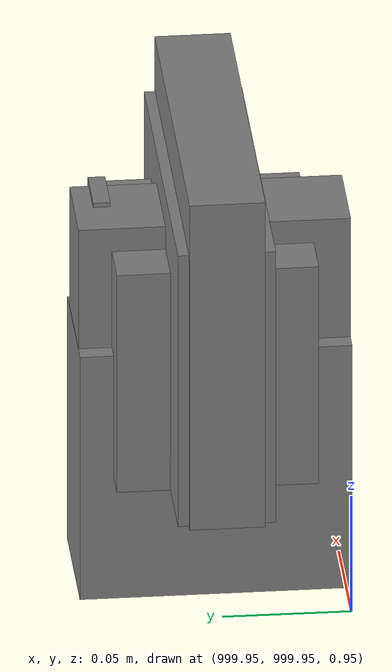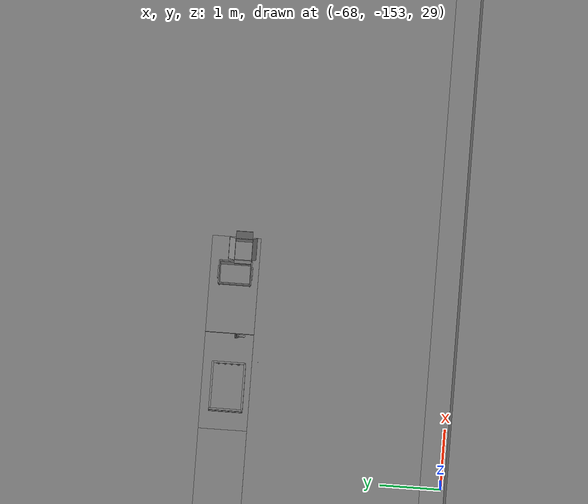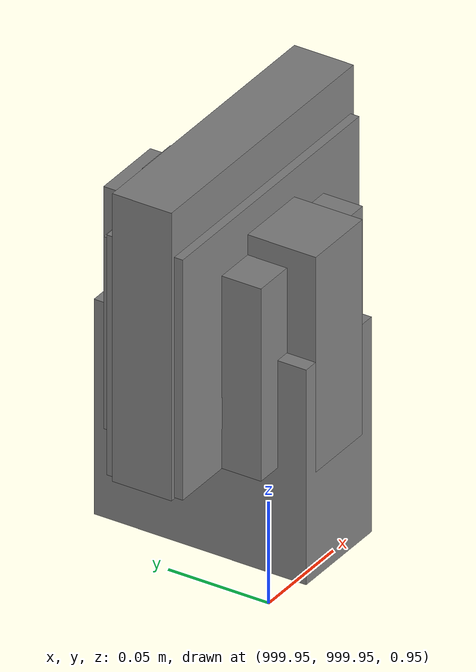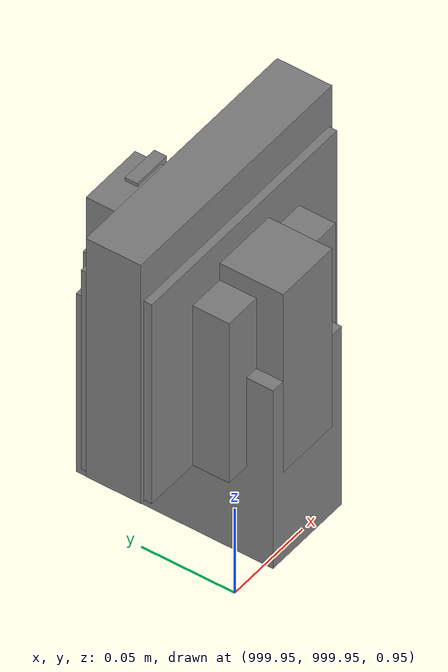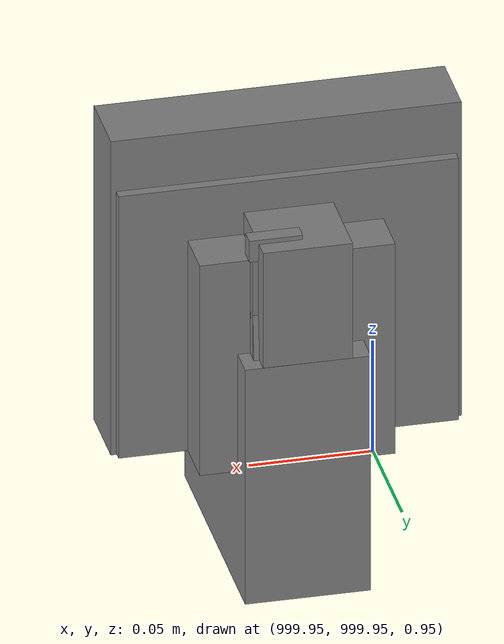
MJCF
<mujoco>
    <option gravity="0.000000000 0.000000000 -9.810000420" timestep="0.0049999999" integrator="implicitfast" density="1.225" viscosity="1.8000001e-05" noslip_iterations="10" iterations="100" sdf_iterations="50">
        <flag multiccd="disable"/>
    </option>
    <size memory="1000M"/>
    <compiler coordinate="local"/>
    <worldbody>
        <light cutoff="30" pos="0 1 1" dir="0 -1 -2"/>
        <light cutoff="30" pos="0 -1 1" dir="0 1 -2"/>
        <body pos="1000.000000000 1000.000000000 1.000000000" euler="0.000011953 0.000005123 -179.999984741" name="openloong_gripper_2f85_fix_base_usda_intel_box">
            <geom contype="1" conaffinity="1" density="1000" type="box" material="" rgba="0.500000000 0.500000000 0.500000000 1.000000000" solimp="0.899999976 0.949999988 0.001000000" friction="1.000000000 0.005000000 0.000100000" solref="0.020000000 1.000000000" margin="0" condim="3" group="0" pos="0.000000000 -0.000067139 0.000082284" quat="0.707106709 0.000000225 0.000000253 0.707106650" size="0.052800003 0.025300000 0.052800003" name="openloong_gripper_2f85_fix_base_usda_geom_90931D53_0DCB_4C76_888E_CD039C37A548"/>
            <freejoint name="openloong_gripper_2f85_fix_base_usda_intel_box_joint"/>
            <site size="0.005000000 0.005000000 0.005000000" rgba="0.500000000 0.500000000 0.500000000 1.000000000" pos="0.000000000 0.000000000 0.000000000" quat="0.999961913 0.008726500 0.000000000 0.000000000" group="0" type="sphere" name="openloong_gripper_2f85_fix_base_usda_intel_boxsite"/>
        </body>
        <body pos="-66.326866150 -149.542068481 31.165672302" euler="-118.910224915 60.714790344 57.124954224" mocap="true" name="spotlight3_SpotLight"/>
        <body pos="1000.000000000 1000.000000000 1.000000000" euler="0.000000000 0.000000000 180.000000000" name="openloong_gripper_2f85_fix_base_usda_battery_01">
            <geom contype="1" conaffinity="1" density="1000" type="box" material="" rgba="0.500000000 0.500000000 0.500000000 1.000000000" solimp="0.899999976 0.949999988 0.001000000" friction="1.000000000 0.005000000 0.000100000" solref="0.020000000 1.000000000" margin="0" condim="3" group="0" pos="-0.011123657 -0.041940309 0.101691343" quat="1.000000000 0.000000000 0.000000000 0.000000000" size="0.010800000 0.003375000 0.004725000" name="openloong_gripper_2f85_fix_base_usda_geom_F34623DC_91D8_4B07_B5D6_64AF7A622C64"/>
            <geom contype="1" conaffinity="1" density="1000" type="box" material="" rgba="0.500000000 0.500000000 0.500000000 1.000000000" solimp="0.899999976 0.949999988 0.001000000" friction="1.000000000 0.005000000 0.000100000" solref="0.020000000 1.000000000" margin="0" condim="3" group="0" pos="-0.010876465 -0.044247437 0.047066893" quat="0.998702705 -0.050920475 0.000000000 0.000000000" size="0.009450001 0.002700000 0.024975000" name="openloong_gripper_2f85_fix_base_usda_geom_ACF7A307_3A4B_423B_9250_D8519870A69D"/>
            <geom contype="1" conaffinity="1" density="1000" type="box" material="" rgba="0.500000000 0.500000000 0.500000000 1.000000000" solimp="0.899999976 0.949999988 0.001000000" friction="1.000000000 0.005000000 0.000100000" solref="0.020000000 1.000000000" margin="0" condim="3" group="0" pos="-0.001235962 -0.000659180 0.047381196" quat="1.000000000 0.000000000 0.000000000 0.000000000" size="0.039420001 0.039150000 0.047250003" name="openloong_gripper_2f85_fix_base_usda_geom_3238FC2F_4587_4B3A_9C0C_8DAA908F11C2"/>
            <geom contype="1" conaffinity="1" density="1000" type="box" material="" rgba="0.500000000 0.500000000 0.500000000 1.000000000" solimp="0.899999976 0.949999988 0.001000000" friction="1.000000000 0.005000000 0.000100000" solref="0.020000000 1.000000000" margin="0" condim="3" group="0" pos="-0.010876465 -0.039138794 0.009851727" quat="1.000000000 0.000000000 0.000000000 0.000000000" size="0.009450001 0.010800000 0.013500000" name="openloong_gripper_2f85_fix_base_usda_geom_1BFF7B0B_AFE7_4F47_8B33_A9D87A930628"/>
            <geom contype="1" conaffinity="1" density="1000" type="box" material="" rgba="0.500000000 0.500000000 0.500000000 1.000000000" solimp="0.899999976 0.949999988 0.001000000" friction="1.000000000 0.005000000 0.000100000" solref="0.020000000 1.000000000" margin="0" condim="3" group="0" pos="-0.010876465 -0.041528322 0.071508206" quat="1.000000000 0.000000000 0.000000000 0.000000000" size="0.009450001 0.002700000 0.027000001" name="openloong_gripper_2f85_fix_base_usda_geom_37F23ED1_594A_4044_AA4C_61D9910BABC1"/>
            <freejoint name="openloong_gripper_2f85_fix_base_usda_battery_01_joint"/>
            <site size="0.005000000 0.005000000 0.005000000" rgba="0.500000000 0.500000000 0.500000000 1.000000000" pos="0.000000000 0.000000000 0.000000000" quat="0.999961913 0.008726500 0.000000000 0.000000000" group="0" type="sphere" name="openloong_gripper_2f85_fix_base_usda_battery_01site"/>
        </body>
        <body pos="1000.000000000 1000.000000000 1.000000000" euler="0.000000000 0.000000000 180.000000000" name="openloong_gripper_2f85_fix_base_usda_cpu_fan">
            <geom contype="1" conaffinity="1" density="1000" type="box" material="" rgba="0.500000000 0.500000000 0.500000000 1.000000000" solimp="0.899999976 0.949999988 0.001000000" friction="1.000000000 0.005000000 0.000100000" solref="0.020000000 1.000000000" margin="0" condim="3" group="0" pos="0.000000000 0.000000000 0.070034981" quat="0.000000000 0.000000000 0.000000000 1.000000000" size="0.070700005 0.014699999 0.070700005" name="openloong_gripper_2f85_fix_base_usda_geom_1D761380_3028_44EE_8DB7_9148D032D48C"/>
            <freejoint name="openloong_gripper_2f85_fix_base_usda_cpu_fan_joint"/>
            <site size="0.005000000 0.005000000 0.005000000" rgba="0.500000000 0.500000000 0.500000000 1.000000000" pos="0.000000000 0.000000000 0.000000000" quat="0.999961913 0.008726535 0.000000000 0.000000000" group="0" type="sphere" name="openloong_gripper_2f85_fix_base_usda_cpu_fancsite"/>
        </body>
        <body pos="-66.261581421 -149.728363037 31.163085938" euler="85.725440979 26.011707306 -115.189796448" mocap="true" name="spotlight6_SpotLight"/>
        <body pos="1000.000000000 1000.000000000 1.000000000" euler="0.000000000 0.000000000 180.000000000" name="openloong_gripper_2f85_fix_base_usda_wifi_box">
            <geom contype="1" conaffinity="1" density="1000" type="box" material="" rgba="0.500000000 0.500000000 0.500000000 1.000000000" solimp="0.899999976 0.949999988 0.001000000" friction="1.000000000 0.005000000 0.000100000" solref="0.020000000 1.000000000" margin="0" condim="3" group="0" pos="0.000000000 0.000000000 0.058978677" quat="0.000000000 0.000000047 0.000000000 1.000000000" size="0.068499997 0.018999999 0.059000000" name="openloong_gripper_2f85_fix_base_usda_geom_4A61F128_DE8E_4CC1_B624_25C6307D42D6"/>
            <freejoint name="openloong_gripper_2f85_fix_base_usda_wifi_box_joint"/>
            <site size="0.005000000 0.005000000 0.005000000" rgba="0.500000000 0.500000000 0.500000000 1.000000000" pos="0.000000000 0.000000000 0.000000000" quat="0.999961913 0.008726500 0.000000000 0.000000000" group="0" type="sphere" name="openloong_gripper_2f85_fix_base_usda_wifi_boxsite"/>
        </body>
        <body pos="1000.000000000 999.999938965 1.000000000" euler="0.000000000 0.000000000 180.000000000" name="openloong_gripper_2f85_fix_base_usda_intelcore_i5">
            <geom contype="1" conaffinity="1" density="1000" type="box" material="" rgba="0.500000000 0.500000000 0.500000000 1.000000000" solimp="0.899999976 0.949999988 0.001000000" friction="1.000000000 0.005000000 0.000100000" solref="0.020000000 1.000000000" margin="0" condim="3" group="0" pos="0.000000000 0.000000000 0.051722717" quat="0.707106709 0.000000000 0.000000000 -0.707106769" size="0.052800000 0.018080002 0.052800000" name="openloong_gripper_2f85_fix_base_usda_geom_AF38AD59_B739_4457_9A16_3929C6EB9D32"/>
            <freejoint name="openloong_gripper_2f85_fix_base_usda_intelcore_i5_joint"/>
            <site size="0.005000000 0.005000000 0.005000000" rgba="0.500000000 0.500000000 0.500000000 1.000000000" pos="0.000000000 0.000000000 0.000000000" quat="0.999961913 0.008726534 0.000000000 0.000000000" group="0" type="sphere" name="openloong_gripper_2f85_fix_base_usda_intelcore_i5site"/>
        </body>
        <body pos="-66.106506348 -149.734756470 31.168762207" euler="-171.837585449 -61.553512573 -10.382506371" mocap="true" name="spotlight4_SpotLight"/>
        <body pos="-64.866622925 -149.383972168 30.183746338" euler="89.999984741 89.999946594 0.000000000" name="openloong_gripper_2f85_fix_base_usda_bluebox_01">
            <geom contype="1" conaffinity="1" density="1000" type="box" material="" rgba="0.500000000 0.500000000 0.500000000 1.000000000" solimp="0.899999976 0.949999988 0.001000000" friction="1.000000000 0.005000000 0.000100000" solref="0.020000000 1.000000000" margin="0" condim="3" group="0" pos="0.276580811 0.187225342 0.000068665" quat="0.707106948 0.000077471 0.707106352 0.000077486" size="0.100000001 0.057999998 0.010000000" name="openloong_gripper_2f85_fix_base_usda_geom_8A90C076_6539_4AA6_ABFB_C8483DAF808B"/>
            <geom contype="1" conaffinity="1" density="1000" type="box" material="" rgba="0.500000000 0.500000000 0.500000000 1.000000000" solimp="0.899999976 0.949999988 0.001000000" friction="1.000000000 0.005000000 0.000100000" solref="0.020000000 1.000000000" margin="0" condim="3" group="0" pos="0.000000000 0.002883911 0.000000000" quat="0.999999881 0.000000000 0.000000000 0.000000000" size="0.254000008 0.003000000 0.172000006" name="openloong_gripper_2f85_fix_base_usda_geom_53D57A4E_3ACE_449E_94BB_09FE405F4D0E"/>
            <geom contype="1" conaffinity="1" density="1000" type="box" material="" rgba="0.500000000 0.500000000 0.500000000 1.000000000" solimp="0.899999976 0.949999988 0.001000000" friction="1.000000000 0.005000000 0.000100000" solref="0.020000000 1.000000000" margin="0" condim="3" group="0" pos="0.000000000 0.124874115 0.173484802" quat="0.999796331 0.020176515 -0.000000015 0.000000030" size="0.259999990 0.119999997 0.007000000" name="openloong_gripper_2f85_fix_base_usda_geom_59F3A10D_0957_4538_AD5B_E749D48BFE8B"/>
            <geom contype="1" conaffinity="1" density="1000" type="box" material="" rgba="0.500000000 0.500000000 0.500000000 1.000000000" solimp="0.899999976 0.949999988 0.001000000" friction="1.000000000 0.005000000 0.000100000" solref="0.020000000 1.000000000" margin="0" condim="3" group="0" pos="0.000000000 0.124874115 -0.173469543" quat="0.999796331 -0.020176545 -0.000000015 0.000000000" size="0.259999990 0.119999997 0.007000000" name="openloong_gripper_2f85_fix_base_usda_geom_526899C9_9F98_4645_A5B5_26E8051A9805"/>
            <geom contype="1" conaffinity="1" density="1000" type="box" material="" rgba="0.500000000 0.500000000 0.500000000 1.000000000" solimp="0.899999976 0.949999988 0.001000000" friction="1.000000000 0.005000000 0.000100000" solref="0.020000000 1.000000000" margin="0" condim="3" group="0" pos="0.000000000 0.214008331 0.188980103" quat="0.999912977 0.013176724 0.000000015 0.000000000" size="0.259999990 0.029999999 0.012500000" name="openloong_gripper_2f85_fix_base_usda_geom_338ABD11_09AE_4A6F_92E4_CABCA43A2284"/>
            <geom contype="1" conaffinity="1" density="1000" type="box" material="" rgba="0.500000000 0.500000000 0.500000000 1.000000000" solimp="0.899999976 0.949999988 0.001000000" friction="1.000000000 0.005000000 0.000100000" solref="0.020000000 1.000000000" margin="0" condim="3" group="0" pos="-0.258361816 0.125289917 0.001876831" quat="0.702796936 -0.020792112 0.710783124 0.020769298" size="0.189999998 0.119999997 0.009000000" name="openloong_gripper_2f85_fix_base_usda_geom_9A6F9905_C1F4_4EAF_B412_74A46B429513"/>
            <geom contype="1" conaffinity="1" density="1000" type="box" material="" rgba="0.500000000 0.500000000 0.500000000 1.000000000" solimp="0.899999976 0.949999988 0.001000000" friction="1.000000000 0.005000000 0.000100000" solref="0.020000000 1.000000000" margin="0" condim="3" group="0" pos="0.000000000 0.214008331 -0.188980103" quat="0.999912977 -0.013176769 0.000000030 0.000000015" size="0.259999990 0.029999999 0.012500000" name="openloong_gripper_2f85_fix_base_usda_geom_0075B10D_987B_4971_B84A_8C8D9510C306"/>
            <geom contype="1" conaffinity="1" density="1000" type="box" material="" rgba="0.500000000 0.500000000 0.500000000 1.000000000" solimp="0.899999976 0.949999988 0.001000000" friction="1.000000000 0.005000000 0.000100000" solref="0.020000000 1.000000000" margin="0" condim="3" group="0" pos="-0.276611328 0.187225342 0.000068665" quat="0.707106650 0.000077441 0.707106709 0.000077456" size="0.100000001 0.057999998 0.010000000" name="openloong_gripper_2f85_fix_base_usda_geom_1DD97554_D20A_41EF_9C42_0BDC4C42E3A5"/>
            <geom contype="1" conaffinity="1" density="1000" type="box" material="" rgba="0.500000000 0.500000000 0.500000000 1.000000000" solimp="0.899999976 0.949999988 0.001000000" friction="1.000000000 0.005000000 0.000100000" solref="0.020000000 1.000000000" margin="0" condim="3" group="0" pos="0.258331299 0.125289917 0.001876831" quat="0.702851415 0.018856421 0.710823774 -0.019329369" size="0.189999998 0.119999997 0.009000000" name="openloong_gripper_2f85_fix_base_usda_geom_AF41D679_02AB_459F_8B80_9337481663A8"/>
            <freejoint name="openloong_gripper_2f85_fix_base_usda_bluebox_01_joint"/>
            <site size="0.005000000 0.005000000 0.005000000" rgba="0.500000000 0.500000000 0.500000000 1.000000000" pos="0.000000000 0.000000000 0.000000000" quat="0.999961913 0.008726534 0.000000000 0.000000000" group="0" type="sphere" name="openloong_gripper_2f85_fix_base_usda_bluebox_01site"/>
        </body>
        <body pos="-64.496299744 -149.491867065 30.235729218" euler="0.000000000 0.000000000 89.999946594" name="openloong_gripper_2f85_fix_base_usda_cardboardbox_01">
            <geom contype="1" conaffinity="1" density="1000" type="box" material="" rgba="0.500000000 0.500000000 0.500000000 1.000000000" solimp="0.899999976 0.949999988 0.001000000" friction="1.000000000 0.005000000 0.000100000" solref="0.020000000 1.000000000" margin="0" condim="3" group="0" pos="-0.003166199 -0.004086494 0.005052090" quat="1.000000000 0.000000000 0.000000000 0.000000000" size="0.142499998 0.177500010 0.005000000" name="openloong_gripper_2f85_fix_base_usda_geom_C51C07C7_FAF2_46EC_89C8_2B3094CFC81F"/>
            <geom contype="1" conaffinity="1" density="1000" type="box" material="" rgba="0.500000000 0.500000000 0.500000000 1.000000000" solimp="0.899999976 0.949999988 0.001000000" friction="1.000000000 0.005000000 0.000100000" solref="0.020000000 1.000000000" margin="0" condim="3" group="0" pos="-0.003166199 0.170316696 0.150570869" quat="1.000000000 0.000000000 0.000000000 0.000000000" size="0.142499998 0.005000000 0.149999991" name="openloong_gripper_2f85_fix_base_usda_geom_93FC36D3_8CF9_4CA6_B489_72C525667A64"/>
            <geom contype="1" conaffinity="1" density="1000" type="box" material="" rgba="0.500000000 0.500000000 0.500000000 1.000000000" solimp="0.899999976 0.949999988 0.001000000" friction="1.000000000 0.005000000 0.000100000" solref="0.020000000 1.000000000" margin="0" condim="3" group="0" pos="-0.147399902 -0.005307198 0.150570869" quat="1.000000000 0.000000000 0.000000000 0.000000000" size="0.005000000 0.177500010 0.149999991" name="openloong_gripper_2f85_fix_base_usda_geom_5F236683_8CF7_45DB_84D9_253832C20AD3"/>
            <geom contype="1" conaffinity="1" density="1000" type="box" material="" rgba="0.500000000 0.500000000 0.500000000 1.000000000" solimp="0.899999976 0.949999988 0.001000000" friction="1.000000000 0.005000000 0.000100000" solref="0.020000000 1.000000000" margin="0" condim="3" group="0" pos="0.140275955 -0.005307198 0.150570869" quat="1.000000000 0.000000000 0.000000000 0.000000000" size="0.005000000 0.177500010 0.149999991" name="openloong_gripper_2f85_fix_base_usda_geom_BCA6B5CE_F4E0_4214_A59B_D1948F31229B"/>
            <geom contype="1" conaffinity="1" density="1000" type="box" material="" rgba="0.500000000 0.500000000 0.500000000 1.000000000" solimp="0.899999976 0.949999988 0.001000000" friction="1.000000000 0.005000000 0.000100000" solref="0.020000000 1.000000000" margin="0" condim="3" group="0" pos="-0.003166199 -0.181550980 0.150570869" quat="1.000000000 0.000000000 0.000000000 0.000000000" size="0.142499998 0.005000000 0.149999991" name="openloong_gripper_2f85_fix_base_usda_geom_4069974A_1BA4_463A_8827_D0989EAD2774"/>
            <freejoint name="openloong_gripper_2f85_fix_base_usda_cardboardbox_01_joint"/>
            <site size="0.005000000 0.005000000 0.005000000" rgba="0.500000000 0.500000000 0.500000000 1.000000000" pos="0.000000000 0.000000000 0.000000000" quat="0.999961913 0.008726535 0.000000000 0.000000000" group="0" type="sphere" name="openloong_gripper_2f85_fix_base_usda_site_052360D0_FB3E_4103_95B3_C46B728B2B74"/>
            <body pos="0.139160156 -0.004048347 0.301930904" euler="-179.999954224 49.383502960 179.999954224" name="openloong_gripper_2f85_fix_base_usda_A1_006">
                <geom contype="1" conaffinity="1" density="1000" type="box" material="" rgba="0.500000000 0.500000000 0.500000000 1.000000000" solimp="0.899999976 0.949999988 0.001000000" friction="1.000000000 0.005000000 0.000100000" solref="0.020000000 1.000000000" margin="0" condim="3" group="0" pos="-0.071587563 0.000009537 0.001745224" quat="0.999999881 0.000000000 0.000000000 0.000000000" size="0.071249999 0.179999992 0.002500000" name="openloong_gripper_2f85_fix_base_usda_geom_89607E84_41EF_431B_B049_156BA36CDE47"/>
                <joint armature="0" stiffness="0.07" damping="0.0099999998" axis="0.000000 1.000000 0.000000" type="hinge" name="openloong_gripper_2f85_fix_base_usda_A1_006"/>
            </body>
            <body pos="-0.145902634 -0.004086494 0.301938057" euler="-180.000000000 -60.000011444 -180.000000000" name="openloong_gripper_2f85_fix_base_usda_A2_006">
                <geom contype="1" conaffinity="1" density="1000" type="box" material="" rgba="0.500000000 0.500000000 0.500000000 1.000000000" solimp="0.899999976 0.949999988 0.001000000" friction="1.000000000 0.005000000 0.000100000" solref="0.020000000 1.000000000" margin="0" condim="3" group="0" pos="0.071268082 0.000009537 0.002717972" quat="0.000002921 0.000000000 -0.000000030 0.999999881" size="0.071249999 0.179999992 0.002500000" name="openloong_gripper_2f85_fix_base_usda_geom_8A270D02_A644_453E_ABF5_2A268C59696B"/>
                <joint armature="0" stiffness="0.07" damping="0.0099999998" axis="0.000000 1.000000 0.000000" type="hinge" name="openloong_gripper_2f85_fix_base_usda_A2_006"/>
            </body>
            <body pos="-0.003385544 0.175991058 0.301930904" euler="-125.858116150 -0.000004561 0.000002331" name="openloong_gripper_2f85_fix_base_usda_B2_006">
                <geom contype="1" conaffinity="1" density="1000" type="box" material="" rgba="0.500000000 0.500000000 0.500000000 1.000000000" solimp="0.899999976 0.949999988 0.001000000" friction="1.000000000 0.005000000 0.000100000" solref="0.020000000 1.000000000" margin="0" condim="3" group="0" pos="0.000009537 -0.070939064 -0.002470016" quat="0.999614120 0.027776197 -0.000000015 0.000000030" size="0.137500003 0.064999998 0.005000000" name="openloong_gripper_2f85_fix_base_usda_geom_942E12FF_A6E3_4552_A4FA_158CCF9E964D"/>
                <joint armature="0" stiffness="0.07" damping="0.0099999998" axis="1.000000 0.000000 0.000000" type="hinge" name="openloong_gripper_2f85_fix_base_usda_B2_006"/>
            </body>
            <body pos="-0.003385544 -0.184140205 0.301938057" euler="147.805557251 0.000000000 0.000000000" name="openloong_gripper_2f85_fix_base_usda_B1_006">
                <geom contype="1" conaffinity="1" density="1000" type="box" material="" rgba="0.500000000 0.500000000 0.500000000 1.000000000" solimp="0.899999976 0.949999988 0.001000000" friction="1.000000000 0.005000000 0.000100000" solref="0.020000000 1.000000000" margin="0" condim="3" group="0" pos="-0.000028610 0.070202351 -0.002703667" quat="0.999614179 -0.027776167 0.000000000 0.000000000" size="0.137500003 0.064999998 0.005000000" name="openloong_gripper_2f85_fix_base_usda_geom_F877BD56_D31A_4980_8C66_A94EF8A92C10"/>
                <joint armature="0" stiffness="0.07" damping="0.0099999998" axis="1.000000 0.000000 0.000000" type="hinge" name="openloong_gripper_2f85_fix_base_usda_B1_006"/>
            </body>
        </body>
        <body pos="-65.882858276 -149.481979370 30.229999542" euler="-64.487716675 0.000000000 0.000000000" name="openloong_gripper_2f85_fix_base_usda_Barcode">
            <geom contype="1" conaffinity="1" density="1000" type="box" material="" rgba="0.500000000 0.500000000 0.500000000 1.000000000" solimp="0.899999976 0.949999988 0.001000000" friction="1.000000000 0.005000000 0.000100000" solref="0.020000000 1.000000000" margin="0" condim="3" group="0" pos="0.000000000 0.013038635 0.001419067" quat="0.000000000 0.000000000 0.000000000 1.000000119" size="0.034000002 0.010000000 0.017999999" name="openloong_gripper_2f85_fix_base_usda_geom_460528D0_CCB1_4609_87B0_E50465F1E192"/>
            <geom contype="1" conaffinity="1" density="1000" type="box" material="" rgba="0.500000000 0.500000000 0.500000000 1.000000000" solimp="0.899999976 0.949999988 0.001000000" friction="1.000000000 0.005000000 0.000100000" solref="0.020000000 1.000000000" margin="0" condim="3" group="0" pos="0.000000000 -0.035301208 -0.007095337" quat="0.000000000 0.000000000 -0.043619365 0.999048233" size="0.028999999 0.010000000 0.020000000" name="openloong_gripper_2f85_fix_base_usda_geom_CDD3C949_52A6_41D9_A8D2_F86193AA0D99"/>
            <geom contype="1" conaffinity="1" density="1000" type="box" material="" rgba="0.500000000 0.500000000 0.500000000 1.000000000" solimp="0.899999976 0.949999988 0.001000000" friction="1.000000000 0.005000000 0.000100000" solref="0.020000000 1.000000000" margin="0" condim="3" group="0" pos="0.000000000 -0.043411255 -0.011749268" quat="0.922262907 0.386563420 0.000000000 0.000000000" size="0.026000001 0.010000000 0.020000000" name="openloong_gripper_2f85_fix_base_usda_geom_545E2AE4_D287_4E3E_923D_9F47FC1D96F1"/>
            <geom contype="1" conaffinity="1" density="1000" type="box" material="" rgba="0.500000000 0.500000000 0.500000000 1.000000000" solimp="0.899999976 0.949999988 0.001000000" friction="1.000000000 0.005000000 0.000100000" solref="0.020000000 1.000000000" margin="0" condim="3" group="0" pos="0.000000000 -0.016967773 -0.031860352" quat="0.000000000 0.000000000 0.000000000 1.000000119" size="0.008000000 0.010000000 0.013000000" name="openloong_gripper_2f85_fix_base_usda_geom_C9A950E4_3EB8_4985_A0F9_4A24B77D4349"/>
            <geom contype="1" conaffinity="1" density="1000" type="box" material="" rgba="0.500000000 0.500000000 0.500000000 1.000000000" solimp="0.899999976 0.949999988 0.001000000" friction="1.000000000 0.005000000 0.000100000" solref="0.020000000 1.000000000" margin="0" condim="3" group="0" pos="0.000000000 -0.001869202 0.000312805" quat="0.953716993 0.300705761 0.000000000 0.000000000" size="0.032000002 0.010000000 0.018999999" name="openloong_gripper_2f85_fix_base_usda_geom_8107855F_196A_4343_B6B0_96A992C84E66"/>
            <geom contype="1" conaffinity="1" density="1000" type="box" material="" rgba="0.500000000 0.500000000 0.500000000 1.000000000" solimp="0.899999976 0.949999988 0.001000000" friction="1.000000000 0.005000000 0.000100000" solref="0.020000000 1.000000000" margin="0" condim="3" group="0" pos="0.000000000 -0.019531250 -0.003173828" quat="0.953716993 0.300705761 0.000000000 0.000000000" size="0.030999999 0.010000000 0.020000000" name="openloong_gripper_2f85_fix_base_usda_geom_8F21367B_6CF9_4609_91D4_F92497142DA3"/>
            <geom contype="1" conaffinity="1" density="1000" type="box" material="" rgba="0.500000000 0.500000000 0.500000000 1.000000000" solimp="0.899999976 0.949999988 0.001000000" friction="1.000000000 0.005000000 0.000100000" solref="0.020000000 1.000000000" margin="0" condim="3" group="0" pos="0.000000000 -0.035301208 -0.007095337" quat="0.953716993 0.300705761 0.000000000 0.000000000" size="0.028999999 0.010000000 0.020000000" name="openloong_gripper_2f85_fix_base_usda_geom_2F289737_7788_4D4D_B288_3BB367EEEEDD"/>
            <geom contype="1" conaffinity="1" density="1000" type="box" material="" rgba="0.500000000 0.500000000 0.500000000 1.000000000" solimp="0.899999976 0.949999988 0.001000000" friction="1.000000000 0.005000000 0.000100000" solref="0.020000000 1.000000000" margin="0" condim="3" group="0" pos="0.000000000 -0.042617798 -0.071121216" quat="0.000000000 0.000000000 0.000000000 1.000000119" size="0.013000000 0.021000000 0.059999999" name="openloong_gripper_2f85_fix_base_usda_geom_74FCD96A_8199_4BAC_A25A_8F49E82C5075"/>
            <freejoint name="openloong_gripper_2f85_fix_base_usda_Barcode_joint"/>
            <site size="0.005000000 0.005000000 0.005000000" rgba="0.500000000 0.500000000 0.500000000 1.000000000" pos="0.000000000 0.000000000 0.000000000" quat="1.000000000 0.000000000 0.000000000 0.000000000" group="0" type="sphere" name="openloong_gripper_2f85_fix_base_usda_Barcode_site"/>
        </body>
        <body pos="-66.745018005 -149.392349243 30.184000015" euler="0.000000000 0.000000000 89.999946594" name="[22330468017438]_Basket_01">
            <geom contype="1" conaffinity="1" density="1000" type="box" material="" rgba="0.500000000 0.500000000 0.500000000 1.000000000" solimp="0.899999976 0.949999988 0.001000000" friction="1.000000000 0.005000000 0.000100000" solref="0.020000000 1.000000000" margin="0" condim="3" group="0" pos="-0.052425385 0.389207840 0.089787483" quat="0.707107008 0.000000000 0.000000000 0.707106411" size="0.014249999 0.014249999 0.059999999" name="[22330468017438]_geom_25FE0E10_A474_4CF7_A0EE_7DE22712EDF5"/>
            <geom contype="1" conaffinity="1" density="1000" type="box" material="" rgba="0.500000000 0.500000000 0.500000000 1.000000000" solimp="0.899999976 0.949999988 0.001000000" friction="1.000000000 0.005000000 0.000100000" solref="0.020000000 1.000000000" margin="0" condim="3" group="0" pos="0.264015198 -0.133043289 0.089787483" quat="0.707107008 0.000000000 0.000000000 0.707106411" size="0.014249999 0.014249999 0.059999999" name="[22330468017438]_geom_153BEC03_0B36_49EE_8B88_066BD6956945"/>
            <geom contype="1" conaffinity="1" density="1000" type="box" material="" rgba="0.500000000 0.500000000 0.500000000 1.000000000" solimp="0.899999976 0.949999988 0.001000000" friction="1.000000000 0.005000000 0.000100000" solref="0.020000000 1.000000000" margin="0" condim="3" group="0" pos="-0.264015198 -0.265548706 0.089793205" quat="0.707107008 0.000000000 0.000000000 0.707106411" size="0.014249999 0.014249999 0.059999999" name="[22330468017438]_geom_F4953225_352B_4D2D_8F2E_E84BBEDC8E74"/>
            <geom contype="1" conaffinity="1" density="1000" type="box" material="" rgba="0.500000000 0.500000000 0.500000000 1.000000000" solimp="0.899999976 0.949999988 0.001000000" friction="1.000000000 0.005000000 0.000100000" solref="0.020000000 1.000000000" margin="0" condim="3" group="0" pos="-0.160263062 -0.389322281 0.089793205" quat="0.707107008 0.000000000 0.000000000 0.707106411" size="0.014249999 0.014249999 0.059999999" name="[22330468017438]_geom_A62A218E_F989_49D7_8F74_414F1D1B0474"/>
            <geom contype="1" conaffinity="1" density="1000" type="box" material="" rgba="0.500000000 0.500000000 0.500000000 1.000000000" solimp="0.899999976 0.949999988 0.001000000" friction="1.000000000 0.005000000 0.000100000" solref="0.020000000 1.000000000" margin="0" condim="3" group="0" pos="0.162265778 -0.389322281 0.089787483" quat="0.707107008 0.000000000 0.000000000 0.707106411" size="0.014249999 0.014249999 0.059999999" name="[22330468017438]_geom_18E1FA7D_0692_41FF_96F1_4E2E53017D0B"/>
            <geom contype="1" conaffinity="1" density="1000" type="box" material="" rgba="0.500000000 0.500000000 0.500000000 1.000000000" solimp="0.899999976 0.949999988 0.001000000" friction="1.000000000 0.005000000 0.000100000" solref="0.020000000 1.000000000" margin="0" condim="3" group="0" pos="0.264015198 0.389207840 0.089787483" quat="0.707107008 0.000000000 0.000000000 0.707106411" size="0.014249999 0.014249999 0.059999999" name="[22330468017438]_geom_373A2188_4B23_4B27_A9C5_2D76B9566625"/>
            <geom contype="1" conaffinity="1" density="1000" type="box" material="" rgba="0.500000000 0.500000000 0.500000000 1.000000000" solimp="0.899999976 0.949999988 0.001000000" friction="1.000000000 0.005000000 0.000100000" solref="0.020000000 1.000000000" margin="0" condim="3" group="0" pos="-0.264015198 -0.133043289 0.089793205" quat="0.707107008 0.000000000 0.000000000 0.707106411" size="0.014249999 0.014249999 0.059999999" name="[22330468017438]_geom_4CD42778_0E5D_403E_AFD9_A3B3ECC72ACE"/>
            <geom contype="1" conaffinity="1" density="1000" type="box" material="" rgba="0.500000000 0.500000000 0.500000000 1.000000000" solimp="0.899999976 0.949999988 0.001000000" friction="1.000000000 0.005000000 0.000100000" solref="0.020000000 1.000000000" margin="0" condim="3" group="0" pos="-0.264026642 0.269256592 0.089793205" quat="0.707107008 0.000000000 0.000000000 0.707106411" size="0.014249999 0.014249999 0.059999999" name="[22330468017438]_geom_8632BEBC_4A83_42AE_AD87_E46212ACE493"/>
            <geom contype="1" conaffinity="1" density="1000" type="box" material="" rgba="0.500000000 0.500000000 0.500000000 1.000000000" solimp="0.899999976 0.949999988 0.001000000" friction="1.000000000 0.005000000 0.000100000" solref="0.020000000 1.000000000" margin="0" condim="3" group="0" pos="0.054462433 0.389207840 0.089787483" quat="0.707107008 0.000000000 0.000000000 0.707106411" size="0.014249999 0.014249999 0.059999999" name="[22330468017438]_geom_2E643E3A_B85E_4A23_B7E7_AFD87B9A0280"/>
            <geom contype="1" conaffinity="1" density="1000" type="box" material="" rgba="0.500000000 0.500000000 0.500000000 1.000000000" solimp="0.899999976 0.949999988 0.001000000" friction="1.000000000 0.005000000 0.000100000" solref="0.020000000 1.000000000" margin="0" condim="3" group="0" pos="0.054462433 -0.389322281 0.089787483" quat="0.707107008 0.000000000 0.000000000 0.707106411" size="0.014249999 0.014249999 0.059999999" name="[22330468017438]_geom_76A93BD3_6E65_4CAB_A8E5_8D5DDAC2C876"/>
            <geom contype="1" conaffinity="1" density="1000" type="box" material="" rgba="0.500000000 0.500000000 0.500000000 1.000000000" solimp="0.899999976 0.949999988 0.001000000" friction="1.000000000 0.005000000 0.000100000" solref="0.020000000 1.000000000" margin="0" condim="3" group="0" pos="0.264015198 0.269256592 0.089793205" quat="0.707107008 0.000000000 0.000000000 0.707106411" size="0.014249999 0.014249999 0.059999999" name="[22330468017438]_geom_B623DCD4_7227_490C_9756_1138803479B8"/>
            <geom contype="1" conaffinity="1" density="1000" type="box" material="" rgba="0.500000000 0.500000000 0.500000000 1.000000000" solimp="0.899999976 0.949999988 0.001000000" friction="1.000000000 0.005000000 0.000100000" solref="0.020000000 1.000000000" margin="0" condim="3" group="0" pos="0.264015198 -0.389322281 0.089787483" quat="0.707107008 0.000000000 0.000000000 0.707106411" size="0.014249999 0.014249999 0.059999999" name="[22330468017438]_geom_D6DD3BA9_218B_40F7_9614_D18DC5A4E3FD"/>
            <geom contype="1" conaffinity="1" density="1000" type="box" material="" rgba="0.500000000 0.500000000 0.500000000 1.000000000" solimp="0.899999976 0.949999988 0.001000000" friction="1.000000000 0.005000000 0.000100000" solref="0.020000000 1.000000000" margin="0" condim="3" group="0" pos="0.000000000 0.000000000 0.015998840" quat="0.707107008 0.000000000 0.000000000 0.707106411" size="0.403499991 0.279000014 0.015750000" name="[22330468017438]_geom_A1328237_5BEB_4B07_A006_8EE2BFA1BD07"/>
            <geom contype="1" conaffinity="1" density="1000" type="box" material="" rgba="0.500000000 0.500000000 0.500000000 1.000000000" solimp="0.899999976 0.949999988 0.001000000" friction="1.000000000 0.005000000 0.000100000" solref="0.020000000 1.000000000" margin="0" condim="3" group="0" pos="0.000000000 -0.389476776 0.163619041" quat="0.707107008 0.000000000 0.000000000 0.707106411" size="0.015000000 0.277500004 0.015750000" name="[22330468017438]_geom_1F0D60D5_829C_4BAA_816B_4591CC5A60FA"/>
            <geom contype="1" conaffinity="1" density="1000" type="box" material="" rgba="0.500000000 0.500000000 0.500000000 1.000000000" solimp="0.899999976 0.949999988 0.001000000" friction="1.000000000 0.005000000 0.000100000" solref="0.020000000 1.000000000" margin="0" condim="3" group="0" pos="0.162265778 0.389207840 0.089787483" quat="0.707107008 0.000000000 0.000000000 0.707106411" size="0.014249999 0.014249999 0.059999999" name="[22330468017438]_geom_9D3FCF6C_0534_4EC2_A0CD_B3A5F71D772E"/>
            <geom contype="1" conaffinity="1" density="1000" type="box" material="" rgba="0.500000000 0.500000000 0.500000000 1.000000000" solimp="0.899999976 0.949999988 0.001000000" friction="1.000000000 0.005000000 0.000100000" solref="0.020000000 1.000000000" margin="0" condim="3" group="0" pos="0.000000000 0.389471054 0.163619041" quat="0.707107008 0.000000000 0.000000000 0.707106411" size="0.015000000 0.277500004 0.015750000" name="[22330468017438]_geom_2048E867_481A_4891_B7A0_BC7D8CB230F4"/>
            <geom contype="1" conaffinity="1" density="1000" type="box" material="" rgba="0.500000000 0.500000000 0.500000000 1.000000000" solimp="0.899999976 0.949999988 0.001000000" friction="1.000000000 0.005000000 0.000100000" solref="0.020000000 1.000000000" margin="0" condim="3" group="0" pos="-0.263511658 0.000000000 0.163619041" quat="0.707107008 0.000000000 0.000000000 0.707106411" size="0.403499991 0.015000000 0.015750000" name="[22330468017438]_geom_74E8BF8F_A941_42FF_8E8A_7C3226A7E04C"/>
            <geom contype="1" conaffinity="1" density="1000" type="box" material="" rgba="0.500000000 0.500000000 0.500000000 1.000000000" solimp="0.899999976 0.949999988 0.001000000" friction="1.000000000 0.005000000 0.000100000" solref="0.020000000 1.000000000" margin="0" condim="3" group="0" pos="-0.264015198 0.141334534 0.089793205" quat="0.707107008 0.000000000 0.000000000 0.707106411" size="0.014249999 0.014249999 0.059999999" name="[22330468017438]_geom_FF14ACE6_E062_4B55_AA60_A7270718D911"/>
            <geom contype="1" conaffinity="1" density="1000" type="box" material="" rgba="0.500000000 0.500000000 0.500000000 1.000000000" solimp="0.899999976 0.949999988 0.001000000" friction="1.000000000 0.005000000 0.000100000" solref="0.020000000 1.000000000" margin="0" condim="3" group="0" pos="0.264015198 -0.265548706 0.089787483" quat="0.707107008 0.000000000 0.000000000 0.707106411" size="0.014249999 0.014249999 0.059999999" name="[22330468017438]_geom_1E2A1D1B_23FF_41DB_8430_F8E19F3FA750"/>
            <geom contype="1" conaffinity="1" density="1000" type="box" material="" rgba="0.500000000 0.500000000 0.500000000 1.000000000" solimp="0.899999976 0.949999988 0.001000000" friction="1.000000000 0.005000000 0.000100000" solref="0.020000000 1.000000000" margin="0" condim="3" group="0" pos="-0.160263062 0.389207840 0.089787483" quat="0.707107008 0.000000000 0.000000000 0.707106411" size="0.014249999 0.014249999 0.059999999" name="[22330468017438]_geom_CE257476_F6EA_48AA_A4A5_DD05A16F8BC6"/>
            <geom contype="1" conaffinity="1" density="1000" type="box" material="" rgba="0.500000000 0.500000000 0.500000000 1.000000000" solimp="0.899999976 0.949999988 0.001000000" friction="1.000000000 0.005000000 0.000100000" solref="0.020000000 1.000000000" margin="0" condim="3" group="0" pos="-0.052425385 -0.389322281 0.089787483" quat="0.707107008 0.000000000 0.000000000 0.707106411" size="0.014249999 0.014249999 0.059999999" name="[22330468017438]_geom_15AF1C94_B09E_4813_954B_94015E4E2C4B"/>
            <geom contype="1" conaffinity="1" density="1000" type="box" material="" rgba="0.500000000 0.500000000 0.500000000 1.000000000" solimp="0.899999976 0.949999988 0.001000000" friction="1.000000000 0.005000000 0.000100000" solref="0.020000000 1.000000000" margin="0" condim="3" group="0" pos="-0.264026642 -0.389322281 0.089793205" quat="0.707107008 0.000000000 0.000000000 0.707106411" size="0.014249999 0.014249999 0.059999999" name="[22330468017438]_geom_FB335867_3A78_4834_B9CE_A191873139AD"/>
            <geom contype="1" conaffinity="1" density="1000" type="box" material="" rgba="0.500000000 0.500000000 0.500000000 1.000000000" solimp="0.899999976 0.949999988 0.001000000" friction="1.000000000 0.005000000 0.000100000" solref="0.020000000 1.000000000" margin="0" condim="3" group="0" pos="0.264015198 0.141334534 0.089787483" quat="0.707107008 0.000000000 0.000000000 0.707106411" size="0.014249999 0.014249999 0.059999999" name="[22330468017438]_geom_09DF3D01_F635_4A36_82AA_2803EAD5114E"/>
            <geom contype="1" conaffinity="1" density="1000" type="box" material="" rgba="0.500000000 0.500000000 0.500000000 1.000000000" solimp="0.899999976 0.949999988 0.001000000" friction="1.000000000 0.005000000 0.000100000" solref="0.020000000 1.000000000" margin="0" condim="3" group="0" pos="-0.264015198 0.389207840 0.089793205" quat="0.707107008 0.000000000 0.000000000 0.707106411" size="0.014249999 0.014249999 0.059999999" name="[22330468017438]_geom_06DCE4A3_0F77_4933_ABC6_8414D71A408A"/>
            <geom contype="1" conaffinity="1" density="1000" type="box" material="" rgba="0.500000000 0.500000000 0.500000000 1.000000000" solimp="0.899999976 0.949999988 0.001000000" friction="1.000000000 0.005000000 0.000100000" solref="0.020000000 1.000000000" margin="0" condim="3" group="0" pos="0.264015198 0.004480362 0.089787483" quat="0.707107008 0.000000000 0.000000000 0.707106411" size="0.014249999 0.014249999 0.059999999" name="[22330468017438]_geom_752F895D_0E0E_41DE_AD02_F8B6BD4292C0"/>
            <geom contype="1" conaffinity="1" density="1000" type="box" material="" rgba="0.500000000 0.500000000 0.500000000 1.000000000" solimp="0.899999976 0.949999988 0.001000000" friction="1.000000000 0.005000000 0.000100000" solref="0.020000000 1.000000000" margin="0" condim="3" group="0" pos="0.263694763 -0.000011444 0.163619041" quat="0.707107008 0.000000000 0.000000000 0.707106411" size="0.403499991 0.015000000 0.015750000" name="[22330468017438]_geom_02C0E3C4_AC7B_4B91_B2FB_9DCD94109813"/>
            <geom contype="1" conaffinity="1" density="1000" type="box" material="" rgba="0.500000000 0.500000000 0.500000000 1.000000000" solimp="0.899999976 0.949999988 0.001000000" friction="1.000000000 0.005000000 0.000100000" solref="0.020000000 1.000000000" margin="0" condim="3" group="0" pos="-0.264015198 0.004480362 0.089793205" quat="0.707107008 0.000000000 0.000000000 0.707106411" size="0.014249999 0.014249999 0.059999999" name="[22330468017438]_geom_14165343_45BF_4AF2_A7E9_3E292D781EF8"/>
            <freejoint name="[22330468017438]_joint_0C4AF7B9_0EDA_497F_AAC1_44B4A6CE92E0"/>
        </body>
        <body pos="0.000000000 0.000000000 0.000000000" euler="0.000000000 0.000000000 0.000000000" name="Static Objects_Static Objects">
            <geom contype="1" conaffinity="1" density="1000" type="box" material="" rgba="0.500000000 0.500000000 0.500000000 1.000000000" solimp="0.899999976 0.949999988 0.001000000" friction="1.000000000 0.005000000 0.000100000" solref="0.020000000 1.000000000" margin="0" condim="3" group="0" pos="-67.544113159 -149.365814209 29.727830887" quat="0.500000417 0.499999970 0.499999553 0.499999970" size="0.381000012 0.319999993 0.041000001" name="Static Objects_geom_CFADBE53_49AF_4CB6_B422_2C2C9B65271B"/>
            <geom contype="1" conaffinity="1" density="1000" type="box" material="" rgba="0.500000000 0.500000000 0.500000000 1.000000000" solimp="0.899999976 0.949999988 0.001000000" friction="1.000000000 0.005000000 0.000100000" solref="0.020000000 1.000000000" margin="0" condim="3" group="0" pos="-68.239501953 -149.365814209 30.086868286" quat="0.500000417 0.499999970 0.499999553 0.499999970" size="0.370999992 0.039500002 0.745000005" name="Static Objects_geom_E94702BD_7BDD_46F5_9CA1_5EF4F9F899D7"/>
            <geom contype="1" conaffinity="1" density="1000" type="box" material="" rgba="0.500000000 0.500000000 0.500000000 1.000000000" solimp="0.899999976 0.949999988 0.001000000" friction="1.000000000 0.005000000 0.000100000" solref="0.020000000 1.000000000" margin="0" condim="3" group="0" pos="-68.239501953 -149.365814209 30.147235870" quat="0.500000417 0.499999970 0.499999553 0.499999970" size="0.400000006 0.022000000 0.800000012" name="Static Objects_geom_720D821B_2B9F_4B62_9B62_2DFBD4BB4FE7"/>
            <geom contype="1" conaffinity="1" density="1000" type="box" material="" rgba="0.500000000 0.500000000 0.500000000 1.000000000" solimp="0.899999976 0.949999988 0.001000000" friction="1.000000000 0.005000000 0.000100000" solref="0.020000000 1.000000000" margin="0" condim="3" group="0" pos="-68.934890747 -149.365814209 29.727830887" quat="0.500000417 0.499999970 0.499999553 0.499999970" size="0.381000012 0.319999993 0.041000001" name="Static Objects_geom_4AF1ACF2_03F0_46B7_98EF_F42A361C6E5B"/>
            <geom contype="1" conaffinity="1" density="1000" type="box" material="" rgba="0.500000000 0.500000000 0.500000000 1.000000000" solimp="0.899999976 0.949999988 0.001000000" friction="1.000000000 0.005000000 0.000100000" solref="0.020000000 1.000000000" margin="0" condim="3" group="0" pos="-68.239501953 -149.365814209 29.561563492" quat="0.500000417 0.499999970 0.499999553 0.499999970" size="0.020000000 0.022000000 0.660000026" name="Static Objects_geom_4567105E_9C9B_4BFD_84D3_A945086CC05E"/>
            <geom contype="1" conaffinity="1" density="1000" type="box" material="" rgba="0.500000000 0.500000000 0.500000000 1.000000000" solimp="0.899999976 0.949999988 0.001000000" friction="1.000000000 0.005000000 0.000100000" solref="0.020000000 1.000000000" margin="0" condim="3" group="0" pos="-65.945671082 -149.365814209 29.727830887" quat="0.500000417 0.499999970 0.499999553 0.499999970" size="0.381000012 0.319999993 0.041000001" name="Static Objects_geom_B0389301_64C6_4243_9E42_5D1A40FA5E1A"/>
            <geom contype="1" conaffinity="1" density="1000" type="box" material="" rgba="0.500000000 0.500000000 0.500000000 1.000000000" solimp="0.899999976 0.949999988 0.001000000" friction="1.000000000 0.005000000 0.000100000" solref="0.020000000 1.000000000" margin="0" condim="3" group="0" pos="-66.641059875 -149.365814209 30.086868286" quat="0.500000417 0.499999970 0.499999553 0.499999970" size="0.370999992 0.039500002 0.745000005" name="Static Objects_geom_FF6678A9_013A_4608_967A_C22E08C8F882"/>
            <geom contype="1" conaffinity="1" density="1000" type="box" material="" rgba="0.500000000 0.500000000 0.500000000 1.000000000" solimp="0.899999976 0.949999988 0.001000000" friction="1.000000000 0.005000000 0.000100000" solref="0.020000000 1.000000000" margin="0" condim="3" group="0" pos="-66.641059875 -149.365814209 30.147235870" quat="0.500000417 0.499999970 0.499999553 0.499999970" size="0.400000006 0.022000000 0.800000012" name="Static Objects_geom_0878323D_494C_4105_85EC_DD144A36F41A"/>
            <geom contype="1" conaffinity="1" density="1000" type="box" material="" rgba="0.500000000 0.500000000 0.500000000 1.000000000" solimp="0.899999976 0.949999988 0.001000000" friction="1.000000000 0.005000000 0.000100000" solref="0.020000000 1.000000000" margin="0" condim="3" group="0" pos="-67.336448669 -149.365814209 29.727830887" quat="0.500000417 0.499999970 0.499999553 0.499999970" size="0.381000012 0.319999993 0.041000001" name="Static Objects_geom_1D888CF2_2A33_4C80_9703_0782C5491299"/>
            <geom contype="1" conaffinity="1" density="1000" type="box" material="" rgba="0.500000000 0.500000000 0.500000000 1.000000000" solimp="0.899999976 0.949999988 0.001000000" friction="1.000000000 0.005000000 0.000100000" solref="0.020000000 1.000000000" margin="0" condim="3" group="0" pos="-66.641059875 -149.365814209 29.561563492" quat="0.500000417 0.499999970 0.499999553 0.499999970" size="0.020000000 0.022000000 0.660000026" name="Static Objects_geom_ED747966_2AF4_4B51_8341_BC7EF99A0F16"/>
            <geom contype="1" conaffinity="1" density="1000" type="box" material="" rgba="0.500000000 0.500000000 0.500000000 1.000000000" solimp="0.899999976 0.949999988 0.001000000" friction="1.000000000 0.005000000 0.000100000" solref="0.020000000 1.000000000" margin="0" condim="3" group="0" pos="-64.338577271 -149.365814209 29.727830887" quat="0.500000417 0.499999970 0.499999553 0.499999970" size="0.381000012 0.319999993 0.041000001" name="Static Objects_geom_F1A14794_229B_4DEC_9CB1_90ACD0E54D1F"/>
            <geom contype="1" conaffinity="1" density="1000" type="box" material="" rgba="0.500000000 0.500000000 0.500000000 1.000000000" solimp="0.899999976 0.949999988 0.001000000" friction="1.000000000 0.005000000 0.000100000" solref="0.020000000 1.000000000" margin="0" condim="3" group="0" pos="-65.033966064 -149.365814209 30.086868286" quat="0.500000417 0.499999970 0.499999553 0.499999970" size="0.370999992 0.039500002 0.745000005" name="Static Objects_geom_FC46DB05_6B8E_4163_BFC7_3DABE673DB81"/>
            <geom contype="1" conaffinity="1" density="1000" type="box" material="" rgba="0.500000000 0.500000000 0.500000000 1.000000000" solimp="0.899999976 0.949999988 0.001000000" friction="1.000000000 0.005000000 0.000100000" solref="0.020000000 1.000000000" margin="0" condim="3" group="0" pos="-65.033966064 -149.365814209 30.147235870" quat="0.500000417 0.499999970 0.499999553 0.499999970" size="0.400000006 0.022000000 0.800000012" name="Static Objects_geom_55FFD8D2_6097_431E_8B03_7845B277449F"/>
            <geom contype="1" conaffinity="1" density="1000" type="box" material="" rgba="0.500000000 0.500000000 0.500000000 1.000000000" solimp="0.899999976 0.949999988 0.001000000" friction="1.000000000 0.005000000 0.000100000" solref="0.020000000 1.000000000" margin="0" condim="3" group="0" pos="-65.729354858 -149.365814209 29.727830887" quat="0.500000417 0.499999970 0.499999553 0.499999970" size="0.381000012 0.319999993 0.041000001" name="Static Objects_geom_DF079C13_27A9_48DD_A607_54519A7F88C3"/>
            <geom contype="1" conaffinity="1" density="1000" type="box" material="" rgba="0.500000000 0.500000000 0.500000000 1.000000000" solimp="0.899999976 0.949999988 0.001000000" friction="1.000000000 0.005000000 0.000100000" solref="0.020000000 1.000000000" margin="0" condim="3" group="0" pos="-65.033966064 -149.365814209 29.561563492" quat="0.500000417 0.499999970 0.499999553 0.499999970" size="0.020000000 0.022000000 0.660000026" name="Static Objects_geom_34BA1059_C68E_4392_AED8_B6EAA305460A"/>
            <geom contype="1" conaffinity="1" density="1000" type="box" material="" rgba="0.500000000 0.500000000 0.500000000 1.000000000" solimp="0.899999976 0.949999988 0.001000000" friction="1.000000000 0.005000000 0.000100000" solref="0.020000000 1.000000000" margin="0" condim="3" group="0" pos="-61.754566193 -137.853729248 33.906845093" quat="0.707107067 0.000000000 0.000000000 0.707106471" size="0.759999990 0.759999990 4.500000000" name="Static Objects_geom_43824C2C_B1A3_4E6C_9D1D_B418F9486A43"/>
            <geom contype="1" conaffinity="1" density="1000" type="box" material="" rgba="0.500000000 0.500000000 0.500000000 1.000000000" solimp="0.899999976 0.949999988 0.001000000" friction="1.000000000 0.005000000 0.000100000" solref="0.020000000 1.000000000" margin="0" condim="3" group="0" pos="-57.511135101 -144.927108765 31.707921982" quat="1.000000000 0.000000000 0.000000000 0.000000000" size="0.200000003 8.000000000 2.299999952" name="Static Objects_geom_46C8777E_7AB6_4FE6_8489_AC6670A14EE0"/>
            <geom contype="1" conaffinity="1" density="1000" type="box" material="" rgba="0.500000000 0.500000000 0.500000000 1.000000000" solimp="0.899999976 0.949999988 0.001000000" friction="1.000000000 0.005000000 0.000100000" solref="0.020000000 1.000000000" margin="0" condim="3" group="0" pos="-80.517646790 -157.574050903 31.688196182" quat="0.707107067 0.000000000 0.000000000 0.707106471" size="0.600000024 0.600000024 2.299999952" name="Static Objects_geom_389E7242_2CE3_4B1B_B47C_D94E40CB51B9"/>
            <geom contype="1" conaffinity="1" density="1000" type="box" material="" rgba="0.500000000 0.500000000 0.500000000 1.000000000" solimp="0.899999976 0.949999988 0.001000000" friction="1.000000000 0.005000000 0.000100000" solref="0.020000000 1.000000000" margin="0" condim="3" group="0" pos="-80.711044312 -147.414932251 31.666158676" quat="1.000000000 0.000000000 0.000000000 0.000000000" size="0.200000003 10.000000000 2.299999952" name="Static Objects_geom_05B41F49_D87A_4622_BA34_014CA13F3DA1"/>
            <geom contype="1" conaffinity="1" density="1000" type="box" material="" rgba="0.500000000 0.500000000 0.500000000 1.000000000" solimp="0.899999976 0.949999988 0.001000000" friction="1.000000000 0.005000000 0.000100000" solref="0.020000000 1.000000000" margin="0" condim="3" group="0" pos="-57.687217712 -137.434692383 31.688196182" quat="0.707107067 0.000000000 0.000000000 0.707106471" size="0.600000024 0.600000024 2.299999952" name="Static Objects_geom_1BAA03BC_96D9_4E0C_B1BD_E2D20E4E467E"/>
            <geom contype="1" conaffinity="1" density="1000" type="box" material="" rgba="0.500000000 0.500000000 0.500000000 1.000000000" solimp="0.899999976 0.949999988 0.001000000" friction="1.000000000 0.005000000 0.000100000" solref="0.020000000 1.000000000" margin="0" condim="3" group="0" pos="-69.537033081 -140.263229370 31.714921951" quat="0.707107067 0.000000000 0.000000000 0.707106471" size="0.759999990 4.500000000 2.299999952" name="Static Objects_geom_1641CB0C_8A80_4038_8F27_0D0B1E1BECAE"/>
            <geom contype="1" conaffinity="1" density="1000" type="box" material="" rgba="0.500000000 0.500000000 0.500000000 1.000000000" solimp="0.899999976 0.949999988 0.001000000" friction="1.000000000 0.005000000 0.000100000" solref="0.020000000 1.000000000" margin="0" condim="3" group="0" pos="-80.073638916 -137.853713989 33.906845093" quat="0.707107067 0.000000000 0.000000000 0.707106471" size="0.759999990 0.759999990 4.500000000" name="Static Objects_geom_FA7F07A0_912E_4948_A266_4AB7EA2C6B81"/>
            <geom contype="1" conaffinity="1" density="1000" type="box" material="" rgba="0.500000000 0.500000000 0.500000000 1.000000000" solimp="0.899999976 0.949999988 0.001000000" friction="1.000000000 0.005000000 0.000100000" solref="0.020000000 1.000000000" margin="0" condim="3" group="0" pos="-73.406707764 -155.734664917 31.707921982" quat="1.000000000 0.000000000 0.000000000 0.000000000" size="0.200000003 3.000000000 2.299999952" name="Static Objects_geom_0D734F95_AF9F_4264_84BB_55BC9366AE0F"/>
            <geom contype="1" conaffinity="1" density="1000" type="box" material="" rgba="0.500000000 0.500000000 0.500000000 1.000000000" solimp="0.899999976 0.949999988 0.001000000" friction="1.000000000 0.005000000 0.000100000" solref="0.020000000 1.000000000" margin="0" condim="3" group="0" pos="-68.497543335 -137.448257446 31.707921982" quat="0.707107067 0.000000000 0.000000000 0.707106471" size="0.200000003 14.000000000 2.299999952" name="Static Objects_geom_9F01C750_C4AB_4928_8F7E_EF5C490A43CB"/>
            <geom contype="1" conaffinity="1" density="1000" type="cylinder" material="" rgba="0.500000000 0.500000000 0.500000000 1.000000000" solimp="0.899999976 0.949999988 0.001000000" friction="1.000000000 0.005000000 0.000100000" solref="0.020000000 1.000000000" margin="0" condim="3" group="0" pos="-68.868522644 -142.134506226 31.711090088" quat="0.707107067 0.000000000 0.000000000 0.707106471" size="0.509999990 2.299999952 1.000000000" name="Static Objects_geom_5BF34B6A_5934_4BCE_A4F2_7D9703F91A04"/>
            <geom contype="1" conaffinity="1" density="1000" type="plane" material="" rgba="0.500000000 0.500000000 0.500000000 1.000000000" solimp="0.899999976 0.949999988 0.001000000" friction="1.000000000 0.005000000 0.000100000" solref="0.020000000 1.000000000" margin="0" condim="3" group="0" pos="-72.873703003 -147.131927490 29.409669876" quat="1.000000000 0.000000000 0.000000000 0.000000000" size="18.000000000 14.000000000 1.000000000" name="Static Objects_geom_F693DF78_1994_4825_8D21_614C911D8143"/>
            <geom contype="1" conaffinity="1" density="1000" type="box" material="" rgba="0.500000000 0.500000000 0.500000000 1.000000000" solimp="0.899999976 0.949999988 0.001000000" friction="1.000000000 0.005000000 0.000100000" solref="0.020000000 1.000000000" margin="0" condim="3" group="0" pos="-79.943580627 -157.782272339 31.707921982" quat="0.707107067 0.000000000 0.000000000 0.707106471" size="0.200000003 7.000000000 2.299999952" name="Static Objects_geom_F9C719EA_334E_4D18_9174_6DE50FF9924C"/>
            <geom contype="1" conaffinity="1" density="1000" type="box" material="" rgba="0.500000000 0.500000000 0.500000000 1.000000000" solimp="0.899999976 0.949999988 0.001000000" friction="1.000000000 0.005000000 0.000100000" solref="0.020000000 1.000000000" margin="0" condim="3" group="0" pos="-65.421028137 -152.903442383 31.707921982" quat="0.707107067 0.000000000 0.000000000 0.707106471" size="0.200000003 7.800000191 2.299999952" name="Static Objects_geom_8C80F868_DFA7_4583_838A_3FC10FD8B81A"/>
            <geom contype="1" conaffinity="1" density="1000" type="box" material="" rgba="0.500000000 0.500000000 0.500000000 1.000000000" solimp="0.899999976 0.949999988 0.001000000" friction="1.000000000 0.005000000 0.000100000" solref="0.020000000 1.000000000" margin="0" condim="3" group="0" pos="-74.776908875 -149.964416504 31.688196182" quat="1.000000000 0.000000000 0.000000000 0.000000000" size="0.600000024 0.409999996 2.299999952" name="Static Objects_geom_80E1701B_195A_4A66_87AC_825977490100"/>
            <geom contype="1" conaffinity="1" density="1000" type="cylinder" material="" rgba="0.500000000 0.500000000 0.500000000 1.000000000" solimp="0.899999976 0.949999988 0.001000000" friction="1.000000000 0.005000000 0.000100000" solref="0.020000000 1.000000000" margin="0" condim="3" group="0" pos="-60.161884308 -142.134506226 31.711090088" quat="0.707107067 0.000000000 0.000000000 0.707106471" size="0.509999990 2.299999952 1.000000000" name="Static Objects_geom_DBB94506_DCBC_4CC8_BEFF_32D265C3FC25"/>
            <geom contype="1" conaffinity="1" density="1000" type="cylinder" material="" rgba="0.500000000 0.500000000 0.500000000 1.000000000" solimp="0.899999976 0.949999988 0.001000000" friction="1.000000000 0.005000000 0.000100000" solref="0.020000000 1.000000000" margin="0" condim="3" group="0" pos="-75.382453918 -149.963455200 31.711090088" quat="0.707107067 0.000000000 0.000000000 0.707106471" size="0.409999996 2.299999952 1.000000000" name="Static Objects_geom_AA3F5FCF_E0BC_47B8_887A_688674EA3F69"/>
            <geom contype="1" conaffinity="1" density="1000" type="cylinder" material="" rgba="0.500000000 0.500000000 0.500000000 1.000000000" solimp="0.899999976 0.949999988 0.001000000" friction="1.000000000 0.005000000 0.000100000" solref="0.020000000 1.000000000" margin="0" condim="3" group="0" pos="-74.154960632 -149.963455200 31.711090088" quat="0.707107067 0.000000000 0.000000000 0.707106471" size="0.409999996 2.299999952 1.000000000" name="Static Objects_geom_FE898823_70C8_41B4_9181_990E3895533F"/>
            <geom contype="1" conaffinity="1" density="1000" type="cylinder" material="" rgba="0.500000000 0.500000000 0.500000000 1.000000000" solimp="0.899999976 0.949999988 0.001000000" friction="1.000000000 0.005000000 0.000100000" solref="0.020000000 1.000000000" margin="0" condim="3" group="0" pos="-77.566612244 -142.134506226 31.711090088" quat="0.707107067 0.000000000 0.000000000 0.707106471" size="0.509999990 2.299999952 1.000000000" name="Static Objects_geom_354EBFE6_C11E_4125_B559_CFA1A1FAC373"/>
        </body>
        <body pos="-66.291030884 -149.869689941 29.018842697" euler="0.000000000 0.000000000 89.999946594" mocap="true" name="openloong_gripper_2f85_fix_base_usda_leftHandMocap"/>
        <body pos="-66.291030884 -149.869689941 29.018842697" euler="0.000000000 0.000000000 89.999946594" mocap="true" name="openloong_gripper_2f85_fix_base_usda_rightHandMocap"/>
        <body pos="-66.291030884 -149.869689941 30.218843460" euler="0.000000000 0.000000000 89.999946594" name="openloong_gripper_2f85_fix_base_usda_base_link">
            <geom contype="1" conaffinity="1" density="1000" type="mesh" material="" rgba="0.783999979 0.783999979 0.783999979 1.000000000" solimp="0.899999976 0.949999988 0.001000000" friction="1.000000000 0.005000000 0.000100000" solref="0.020000000 1.000000000" margin="0" condim="3" group="3" mesh="base_link" pos="0.000000000 0.000000000 0.000000000" quat="1.000000000 0.000000000 0.000000000 0.000000000" size="1.000000000 1.000000000 1.000000000" name="openloong_gripper_2f85_fix_base_usda__geom_7_AA04FB06_FFC6_4A51_9177_08EEBDE49685"/>
            <site size="0.005000000 0.005000000 0.005000000" rgba="0.500000000 0.500000000 0.500000000 1.000000000" pos="0.000000000 0.000000000 0.000000000" quat="1.000000000 0.000000000 0.000000000 0.000000000" group="0" type="sphere" name="openloong_gripper_2f85_fix_base_usda_imu"/>
            <inertial mass="22.447001" pos="-0.005664100 -0.001336700 0.238289997" diaginertia="0.374352545 0.277180195 0.220617250" quat="0.999247074 0.035235517 -0.015086859 0.006023135"/>
            <body pos="0.000000000 0.000000000 0.299997330" euler="0.000000000 0.000000000 0.000000000" name="openloong_gripper_2f85_fix_base_usda_dummy_body">
                <geom contype="1" conaffinity="1" density="1000" type="sphere" material="" rgba="0.783999979 0.783999979 0.783999979 1.000000000" solimp="0.899999976 0.949999988 0.001000000" friction="1.000000000 0.005000000 0.000100000" solref="0.020000000 1.000000000" margin="0" condim="3" group="3" pos="0.000000000 0.000000000 0.000000000" quat="1.000000000 0.000000000 0.000000000 0.000000000" size="0.010000000 0.000000000 0.000000000" name="openloong_gripper_2f85_fix_base_usda__geom_8_A6AC127A_1A7A_432E_86F1_1AC10FDA6C8E"/>
                <joint armature="0.0099999998" stiffness="0" damping="0.1" axis="0.000000 0.000000 1.000000" type="hinge" name="openloong_gripper_2f85_fix_base_usda_dummy_joint"/>
                <site size="0.010000000 0.005000000 0.005000000" rgba="0.500000000 0.500000000 0.500000000 1.000000000" pos="0.000000000 0.000000000 0.000000000" quat="1.000000000 0.000000000 0.000000000 0.000000000" group="3" type="sphere" name="openloong_gripper_2f85_fix_base_usda_dummy_site"/>
            </body>
            <body pos="0.009002686 0.000000000 0.406400681" euler="0.000000000 0.000000000 0.000000000" name="openloong_gripper_2f85_fix_base_usda_Link_head_yaw">
                <geom contype="1" conaffinity="1" density="1000" type="mesh" material="" rgba="0.783999979 0.783999979 0.783999979 1.000000000" solimp="0.899999976 0.949999988 0.001000000" friction="1.000000000 0.005000000 0.000100000" solref="0.020000000 1.000000000" margin="0" condim="3" group="3" mesh="Link_head_yaw" pos="0.000000000 0.000000000 0.000000000" quat="1.000000000 0.000000000 0.000000000 0.000000000" size="1.000000000 1.000000000 1.000000000" name="openloong_gripper_2f85_fix_base_usda__geom_10_F7D6A9B7_98D6_4776_A5AF_807BA44459F2"/>
                <inertial mass="0.84249002" pos="0.000000000 -0.002081400 0.044801001" diaginertia="0.000700588 0.000629000 0.000553812" quat="0.706933022 -0.015675601 0.015677100 0.706933022"/>
                <body pos="0.000000000 -0.034599304 0.048500061" euler="0.000000000 0.000000000 0.000000000" name="openloong_gripper_2f85_fix_base_usda_Link_head_pitch">
                    <geom contype="1" conaffinity="1" density="1000" type="mesh" material="" rgba="0.783999979 0.783999979 0.783999979 1.000000000" solimp="0.899999976 0.949999988 0.001000000" friction="1.000000000 0.005000000 0.000100000" solref="0.020000000 1.000000000" margin="0" condim="3" group="3" mesh="Link_head_pitch" pos="0.000000000 0.000000000 0.000000000" quat="1.000000000 0.000000000 0.000000000 0.000000000" size="1.000000000 1.000000000 1.000000000" name="openloong_gripper_2f85_fix_base_usda__geom_12_4EDE65B4_945D_4401_B4B3_12FA30613E02"/>
                    <inertial mass="1.3943" pos="0.020569000 0.033004001 0.125000000" diaginertia="0.006381400 0.006289940 0.004481460" quat="0.973390222 0.008406822 0.228157058 0.019624906"/>
                    <body pos="0.000000000 0.029998779 0.000000000" euler="0.000000000 0.000000000 0.000000000" name="openloong_gripper_2f85_fix_base_usda_neck_center_body">
                        <site size="0.010000000 0.005000000 0.005000000" rgba="0.500000000 0.500000000 0.500000000 1.000000000" pos="0.000000000 0.000000000 0.000000000" quat="1.000000000 0.000000000 0.000000000 0.000000000" group="3" type="sphere" name="openloong_gripper_2f85_fix_base_usda_neck_center_site"/>
                        <body pos="0.020004272 0.000000000 0.149999619" euler="-0.000002229 39.998176575 -90.000205994" name="openloong_gripper_2f85_fix_base_usda_camera_head">
                            <site size="0.010000000 0.005000000 0.005000000" rgba="0.500000000 0.500000000 0.500000000 1.000000000" pos="0.000000000 0.000000000 0.000000000" quat="1.000000000 0.000000000 0.000000000 0.000000000" group="3" type="sphere" name="openloong_gripper_2f85_fix_base_usda_camera_head_site"/>
                        </body>
                    </body>
                </body>
            </body>
            <body pos="0.003997803 -0.161598206 0.392200470" euler="0.000000000 0.000000000 0.000000000" name="openloong_gripper_2f85_fix_base_usda_Link_arm_r_01">
                <geom contype="1" conaffinity="1" density="1000" type="mesh" material="" rgba="0.783999979 0.783999979 0.783999979 1.000000000" solimp="0.899999976 0.949999988 0.001000000" friction="1.000000000 0.005000000 0.000100000" solref="0.020000000 1.000000000" margin="0" condim="3" group="3" mesh="Link_arm_r_01" pos="0.000000000 0.000000000 0.000000000" quat="1.000000000 0.000000000 0.000000000 0.000000000" size="1.000000000 1.000000000 1.000000000" name="openloong_gripper_2f85_fix_base_usda__geom_14_46455041_C71C_4E74_812A_80017C1384BA"/>
                <joint armature="0.0099999998" stiffness="0" damping="1" axis="0.000000 -1.000000 0.000000" limited="true" range="-170.000015259 170.000015259" type="hinge" name="openloong_gripper_2f85_fix_base_usda_J_arm_r_01"/>
                <inertial mass="0.75641" pos="0.004494600 -0.038293999 -0.000001874" diaginertia="0.000842990 0.000803050 0.000587120" quat="-0.000163502 0.707098067 0.000812463 0.707115054"/>
                <body pos="-0.041992188 -0.041000366 0.000000000" euler="0.000000000 0.000000000 0.000000000" name="openloong_gripper_2f85_fix_base_usda_Link_arm_r_02">
                    <geom contype="1" conaffinity="1" density="1000" type="mesh" material="" rgba="0.783999979 0.783999979 0.783999979 1.000000000" solimp="0.899999976 0.949999988 0.001000000" friction="1.000000000 0.005000000 0.000100000" solref="0.020000000 1.000000000" margin="0" condim="3" group="3" mesh="Link_arm_r_02" pos="0.000000000 0.000000000 0.000000000" quat="1.000000000 0.000000000 0.000000000 0.000000000" size="1.000000000 1.000000000 1.000000000" name="openloong_gripper_2f85_fix_base_usda__geom_16_5D00108B_2C8B_45E1_BC26_3BBA91587294"/>
                    <joint armature="0.0099999998" stiffness="0" damping="1" axis="-1.000000 0.000000 0.000000" limited="true" range="-105.000244141 105.000244141" type="hinge" name="openloong_gripper_2f85_fix_base_usda_J_arm_r_02"/>
                    <inertial mass="0.98500001" pos="0.041999999 -0.067430697 0.000000000" diaginertia="0.002262690 0.001730990 0.001154020" quat="0.500000000 0.500000000 -0.500000000 0.500000000"/>
                    <body pos="0.041992188 -0.122596741 0.000000000" euler="0.000000000 0.000000000 0.000000000" name="openloong_gripper_2f85_fix_base_usda_Link_arm_r_03">
                        <geom contype="1" conaffinity="1" density="1000" type="mesh" material="" rgba="0.783999979 0.783999979 0.783999979 1.000000000" solimp="0.899999976 0.949999988 0.001000000" friction="1.000000000 0.005000000 0.000100000" solref="0.020000000 1.000000000" margin="0" condim="3" group="3" mesh="Link_arm_r_03" pos="0.000000000 0.000000000 0.000000000" quat="1.000000000 0.000000000 0.000000000 0.000000000" size="1.000000000 1.000000000 1.000000000" name="openloong_gripper_2f85_fix_base_usda__geom_18_8488B2E2_A8C7_4C0F_B917_E5879CBF6C0B"/>
                        <joint armature="0.0099999998" stiffness="0" damping="1" axis="0.000000 -1.000000 0.000000" limited="true" range="-170.000015259 170.000015259" type="hinge" name="openloong_gripper_2f85_fix_base_usda_J_arm_r_03"/>
                        <inertial mass="0.95899999" pos="-0.001413580 -0.164663002 0.020757901" diaginertia="0.002101340 0.002064590 0.000754802" quat="0.560480952 0.454391927 -0.443732947 0.531497955"/>
                        <body pos="0.035293579 -0.177406311 0.023998260" euler="0.000000000 0.000000000 0.000000000" name="openloong_gripper_2f85_fix_base_usda_Link_arm_r_04">
                            <geom contype="1" conaffinity="1" density="1000" type="mesh" material="" rgba="0.783999979 0.783999979 0.783999979 1.000000000" solimp="0.899999976 0.949999988 0.001000000" friction="1.000000000 0.005000000 0.000100000" solref="0.020000000 1.000000000" margin="0" condim="3" group="3" mesh="Link_arm_r_04" pos="0.000000000 0.000000000 0.000000000" quat="1.000000000 0.000000000 0.000000000 0.000000000" size="1.000000000 1.000000000 1.000000000" name="openloong_gripper_2f85_fix_base_usda__geom_20_78F6FBB9_5263_4E37_BA09_E84A546F8E5C"/>
                            <joint armature="0.0099999998" stiffness="0" damping="1" axis="-1.000000 0.000000 0.000000" limited="true" range="0.000000000 170.000015259" type="hinge" name="openloong_gripper_2f85_fix_base_usda_J_arm_r_04"/>
                            <inertial mass="0.60000002" pos="-0.038727000 -0.060766999 -0.021003000" diaginertia="0.001092610 0.000712422 0.000645102" quat="0.327701002 0.632602990 -0.467366993 0.523443997"/>
                            <body pos="-0.035293579 -0.103492737 -0.023998260" euler="0.000000000 0.000000000 0.000000000" name="openloong_gripper_2f85_fix_base_usda_Link_arm_r_05">
                                <geom contype="1" conaffinity="1" density="1000" type="mesh" material="" rgba="0.783999979 0.783999979 0.783999979 1.000000000" solimp="0.899999976 0.949999988 0.001000000" friction="1.000000000 0.005000000 0.000100000" solref="0.020000000 1.000000000" margin="0" condim="3" group="3" mesh="Link_arm_r_05" pos="0.000000000 0.000000000 0.000000000" quat="1.000000000 0.000000000 0.000000000 0.000000000" size="1.000000000 1.000000000 1.000000000" name="openloong_gripper_2f85_fix_base_usda__geom_22_3915706A_883F_4CAB_ADB7_96115095B88C"/>
                                <joint armature="0.0099999998" stiffness="0" damping="1" axis="0.000000 -1.000000 0.000000" limited="true" range="-170.000015259 170.000015259" type="hinge" name="openloong_gripper_2f85_fix_base_usda_J_arm_r_05"/>
                                <inertial mass="0.68976003" pos="0.000032712 -0.068658002 -0.000111780" diaginertia="0.002522510 0.002411100 0.000448695" quat="0.707660973 0.706543028 -0.002603360 0.002470550"/>
                                <body pos="-0.026489258 -0.196502686 0.000000000" euler="0.000000000 0.000000000 0.000000000" name="openloong_gripper_2f85_fix_base_usda_Link_arm_r_06">
                                    <geom contype="1" conaffinity="1" density="1000" type="mesh" material="" rgba="0.783999979 0.783999979 0.783999979 1.000000000" solimp="0.899999976 0.949999988 0.001000000" friction="1.000000000 0.005000000 0.000100000" solref="0.020000000 1.000000000" margin="0" condim="3" group="3" mesh="Link_arm_r_06" pos="0.000000000 0.000000000 0.000000000" quat="1.000000000 0.000000000 0.000000000 0.000000000" size="1.000000000 1.000000000 1.000000000" name="openloong_gripper_2f85_fix_base_usda__geom_24_30A3384C_419F_46BA_BDB5_1C5E1FC80E55"/>
                                    <joint armature="0.0099999998" stiffness="0" damping="1" axis="1.000000 0.000000 0.000000" limited="true" range="-105.000244141 105.000244141" type="hinge" name="openloong_gripper_2f85_fix_base_usda_J_arm_r_06"/>
                                    <inertial mass="0.28" pos="0.026078001 -0.000000896 0.001663700" diaginertia="0.000156930 0.000145601 0.000104979" quat="0.707080841 0.001851080 0.001883810 0.707127810"/>
                                    <body pos="0.026489258 0.000000000 0.031799316" euler="0.000000000 0.000000000 0.000000000" name="openloong_gripper_2f85_fix_base_usda_Link_arm_r_07">
                                        <geom contype="1" conaffinity="1" density="1000" type="mesh" material="" rgba="0.783999979 0.783999979 0.783999979 1.000000000" solimp="0.899999976 0.949999988 0.001000000" friction="1.000000000 0.005000000 0.000100000" solref="0.020000000 1.000000000" margin="0" condim="3" group="3" mesh="Link_arm_r_07" pos="0.000000000 0.000000000 0.000000000" quat="1.000000000 0.000000000 0.000000000 0.000000000" size="1.000000000 1.000000000 1.000000000" name="openloong_gripper_2f85_fix_base_usda__geom_26_EF0A6C78_8FEB_459A_A859_34AFE6E0708C"/>
                                        <joint armature="0.0099999998" stiffness="0" damping="1" axis="0.000000 0.000000 1.000000" limited="true" range="-60.000133514 60.000133514" type="hinge" name="openloong_gripper_2f85_fix_base_usda_J_arm_r_07"/>
                                        <inertial mass="0.61353999" pos="-0.007859000 -0.158170000 -0.027736001" diaginertia="0.003037610 0.002570910 0.000729379" quat="0.427542925 0.443532884 -0.553093910 0.560867906"/>
                                        <body pos="0.000000000 0.286994934 -0.270000458" euler="150.000350952 -0.000001649 -0.000000442" name="openloong_gripper_2f85_fix_base_usda_camera_wrist_r">
                                            <site size="0.010000000 0.005000000 0.005000000" rgba="0.500000000 0.500000000 0.500000000 1.000000000" pos="0.000000000 0.000000000 0.000000000" quat="1.000000000 0.000000000 0.000000000 0.000000000" group="3" type="sphere" name="openloong_gripper_2f85_fix_base_usda_camera_wrist_r_site"/>
                                        </body>
                                        <body pos="0.000000000 -0.220008850 -0.033002853" euler="0.000000000 0.000000000 179.999969482" name="openloong_gripper_2f85_fix_base_usda_ee_center_body_r">
                                            <site size="0.010000000 0.005000000 0.005000000" rgba="0.500000000 0.500000000 0.500000000 1.000000000" pos="0.000000000 0.000000000 0.000000000" quat="1.000000000 0.000000000 0.000000000 0.000000000" group="3" type="sphere" name="openloong_gripper_2f85_fix_base_usda_ee_center_site_r"/>
                                        </body>
                                        <body pos="0.000000000 -0.066001892 -0.031000137" euler="89.999984741 0.000000000 180.000000000" name="openloong_gripper_2f85_fix_base_usda_zbr_base_link">
                                            <geom contype="1" conaffinity="1" density="1000" type="mesh" material="" rgba="0.783999979 0.783999979 0.783999979 1.000000000" solimp="0.899999976 0.949999988 0.001000000" friction="1.000000000 0.005000000 0.000100000" solref="0.020000000 1.000000000" margin="0" condim="3" group="3" mesh="base" pos="0.000000000 0.000003815 -0.000007629" quat="1.000000000 0.000000000 0.000000000 0.000000000" size="1.000000238 1.000000238 1.000000238" name="openloong_gripper_2f85_fix_base_usda__geom_30_DEDF2F80_7699_4E85_8A8F_D55CBFF936B8"/>
                                            <inertial mass="0.77744102" pos="0.000000000 -0.000027039 0.035467502" diaginertia="0.000260285 0.000225381 0.000152708" quat="0.999998808 -0.001528488 0.000000000 0.000000000"/>
                                            <body pos="-0.030609138 0.004745484 0.065696731" euler="-89.999984741 -0.000000000 0.000000000" name="openloong_gripper_2f85_fix_base_usda_r_left_driver">
                                                <geom contype="1" conaffinity="1" density="1000" type="mesh" material="" rgba="0.783999979 0.783999979 0.783999979 1.000000000" solimp="0.899999976 0.949999988 0.001000000" friction="1.000000000 0.005000000 0.000100000" solref="0.020000000 1.000000000" margin="0" condim="3" group="3" mesh="driver" pos="0.030609138 0.054901138 -0.004699708" quat="0.707106829 0.707106709 0.000000000 -0.000000000" size="1.000000238 1.000000238 1.000000238" name="openloong_gripper_2f85_fix_base_usda__geom_32_D87D8FD8_BD46_46CA_ACD6_557590183924"/>
                                                <joint armature="0.0049999999" stiffness="0" damping="0.1" axis="0.000000 0.000000 1.000000" limited="true" range="0.000000000 51.566200256" type="hinge" name="openloong_gripper_2f85_fix_base_usda_r_left_driver_joint"/>
                                                <inertial mass="0.0089956298" pos="0.000000000 0.017754700 0.001073140" diaginertia="0.000001724 0.000001609 0.000000322" quat="0.681301236 0.732003212 0.000000000 0.000000000"/>
                                                <body pos="-0.031402595 0.004524232 -0.010200503" euler="0.000000000 0.000000000 180.000000000" name="openloong_gripper_2f85_fix_base_usda_r_left_coupler">
                                                    <geom contype="1" conaffinity="1" density="1000" type="mesh" material="" rgba="0.783999979 0.783999979 0.783999979 1.000000000" solimp="0.899999976 0.949999988 0.001000000" friction="1.000000000 0.005000000 0.000100000" solref="0.020000000 1.000000000" margin="0" condim="3" group="3" mesh="coupler" pos="-0.062011734 -0.050354015 0.005500795" quat="0.707106829 -0.707106709 0.000000000 -0.000000000" size="1.000000238 1.000000238 1.000000238" name="openloong_gripper_2f85_fix_base_usda__geom_34_C8245D3A_CFC0_4E76_BDF5_ED8004344C0A"/>
                                                    <inertial mass="0.0140974" pos="0.000000000 0.003012090 0.023217499" diaginertia="0.000004162 0.000003522 0.000000888" quat="0.705635548 -0.045590367 0.045590367 0.705635548"/>
                                                </body>
                                            </body>
                                            <body pos="-0.012695315 -0.012001040 0.072212234" euler="-89.999984741 -0.000000000 0.000000000" name="openloong_gripper_2f85_fix_base_usda_r_left_spring_link">
                                                <geom contype="1" conaffinity="1" density="1000" type="mesh" material="" rgba="0.783999979 0.783999979 0.783999979 1.000000000" solimp="0.899999976 0.949999988 0.001000000" friction="1.000000000 0.005000000 0.000100000" solref="0.020000000 1.000000000" margin="0" condim="3" group="3" mesh="spring_link" pos="0.012695315 0.061416641 0.012050631" quat="0.707106829 0.707106709 0.000000000 -0.000000000" size="1.000000238 1.000000238 1.000000238" name="openloong_gripper_2f85_fix_base_usda__geom_36_0CAFA84B_2BAA_48A8_9E8C_74AC2867FA36"/>
                                                <joint armature="0.001" stiffness="0.050000001" damping="0.00125" axis="0.000000 0.000000 1.000000" limited="true" range="-17.000000000 51.566200256" type="hinge" name="openloong_gripper_2f85_fix_base_usda_r_left_spring_link_joint"/>
                                                <inertial mass="0.0221642" pos="-0.000000009 0.018162400 0.021265799" diaginertia="0.000008969 0.000006717 0.000002639" quat="0.663403213 -0.244737089 0.244737089 0.663403213"/>
                                                <body pos="-0.038208015 -0.042503368 0.002950669" euler="180.000000000 0.000000000 -0.002185660" name="openloong_gripper_2f85_fix_base_usda_r_left_follower">
                                                    <geom contype="1" conaffinity="1" density="1000" type="mesh" material="" rgba="0.783999979 0.783999979 0.783999979 1.000000000" solimp="0.899999976 0.949999988 0.001000000" friction="1.000000000 0.005000000 0.000100000" solref="0.020000000 1.000000000" margin="0" condim="3" group="3" mesh="tongue" pos="0.050918590 -0.103920005 -0.009099962" quat="0.707106829 -0.707106709 0.000000030 0.000000030" size="1.000000238 1.000000238 1.000000238" name="openloong_gripper_2f85_fix_base_usda__geom_40_67548A2D_BE60_46FD_AA58_77EFFF430D6B"/>
                                                    <geom contype="1" conaffinity="1" density="1000" type="mesh" material="" rgba="0.783999979 0.783999979 0.783999979 1.000000000" solimp="0.899999976 0.949999988 0.001000000" friction="1.000000000 0.005000000 0.000100000" solref="0.020000000 1.000000000" margin="0" condim="3" group="3" mesh="follower" pos="0.050918590 -0.103920005 -0.009099962" quat="0.707106829 -0.707106709 0.000000030 0.000000030" size="1.000000238 1.000000238 1.000000238" name="openloong_gripper_2f85_fix_base_usda__geom_39_2C90371D_3AF0_4AB5_911F_A1BE777A0579"/>
                                                    <joint armature="0.001" stiffness="0" damping="0.1" axis="0.000000 0.000000 1.000000" limited="true" range="-49.999961853 51.566200256" type="hinge" name="openloong_gripper_2f85_fix_base_usda_r_left_follower"/>
                                                    <inertial mass="0.0125222" pos="0.000000000 -0.011046000 0.012478600" diaginertia="0.000002674 0.000002456 0.000000602" quat="0.986436546 0.164143041 0.000000000 0.000000000"/>
                                                    <body pos="-0.037765510 -0.103912376 -0.009099962" euler="-89.999984741 0.000000000 0.000004829" name="openloong_gripper_2f85_fix_base_usda_r_left_pad">
                                                        <geom contype="1" conaffinity="1" density="1000" type="box" material="" rgba="0.550000012 0.550000012 0.550000012 1.000000000" solimp="0.949999988 0.990000010 0.001000000" friction="0.699999988 0.005000000 0.000100000" solref="0.020000000 1.000000000" margin="0" condim="3" group="3" mass="1e-06" pos="0.043243419 0.000003815 0.119995147" quat="0.999999881 0.000000000 0.000000000 0.000000000" size="0.002000001 0.011000003 0.009375002" name="openloong_gripper_2f85_fix_base_usda_r_left_pad1_DBE670AA_FE1A_4A72_BEF7_3788A7923486"/>
                                                        <geom contype="1" conaffinity="1" density="1000" type="box" material="" rgba="0.449999988 0.449999988 0.449999988 1.000000000" solimp="0.949999988 0.990000010 0.001000000" friction="0.600000024 0.005000000 0.000100000" solref="0.020000000 1.000000000" margin="0" condim="3" group="3" mass="1e-06" pos="0.043243419 0.000003815 0.138748199" quat="0.999999881 0.000000000 0.000000000 0.000000000" size="0.002000001 0.011000003 0.009375002" name="openloong_gripper_2f85_fix_base_usda_r_left_pad2_F8342297_8B91_4D2E_90FB_883C5D3C4D83"/>
                                                    </body>
                                                </body>
                                            </body>
                                            <body pos="0.030593880 -0.004753114 0.065696731" euler="89.999984741 0.000000000 180.000000000" name="openloong_gripper_2f85_fix_base_usda_r_right_driver">
                                                <geom contype="1" conaffinity="1" density="1000" type="mesh" material="" rgba="0.783999979 0.783999979 0.783999979 1.000000000" solimp="0.899999976 0.949999988 0.001000000" friction="1.000000000 0.005000000 0.000100000" solref="0.020000000 1.000000000" margin="0" condim="3" group="3" mesh="driver" pos="0.030593880 0.054901138 -0.004699708" quat="0.707106829 0.707106709 0.000000000 0.000000000" size="1.000000238 1.000000238 1.000000238" name="openloong_gripper_2f85_fix_base_usda__geom_42_B1ACFFBF_3C06_41CC_A60A_BFA5B756BF13"/>
                                                <joint armature="0.0049999999" stiffness="0" damping="0.1" axis="0.000000 0.000000 1.000000" limited="true" range="0.000000000 51.566200256" type="hinge" name="openloong_gripper_2f85_fix_base_usda_r_right_driver_joint"/>
                                                <inertial mass="0.0089956298" pos="0.000000000 0.017754700 0.001073140" diaginertia="0.000001724 0.000001609 0.000000322" quat="0.681301236 0.732003212 0.000000000 0.000000000"/>
                                                <body pos="-0.031417854 0.004531861 -0.010202411" euler="0.000000000 0.000000000 180.000000000" name="openloong_gripper_2f85_fix_base_usda_r_right_coupler">
                                                    <geom contype="1" conaffinity="1" density="1000" type="mesh" material="" rgba="0.783999979 0.783999979 0.783999979 1.000000000" solimp="0.899999976 0.949999988 0.001000000" friction="1.000000000 0.005000000 0.000100000" solref="0.020000000 1.000000000" margin="0" condim="3" group="3" mesh="coupler" pos="-0.062042251 -0.050376903 0.005500795" quat="0.707106829 -0.707106709 0.000000000 0.000000000" size="1.000000238 1.000000238 1.000000238" name="openloong_gripper_2f85_fix_base_usda__geom_44_C5BA5774_8113_4851_B0F8_6D20FC484BF9"/>
                                                    <inertial mass="0.0140974" pos="0.000000000 0.003012090 0.023217499" diaginertia="0.000004162 0.000003522 0.000000888" quat="0.705635548 -0.045590367 0.045590367 0.705635548"/>
                                                </body>
                                            </body>
                                            <body pos="0.012695315 0.011997226 0.072219864" euler="89.999984741 0.000000000 180.000000000" name="openloong_gripper_2f85_fix_base_usda_r_right_spring_link">
                                                <geom contype="1" conaffinity="1" density="1000" type="mesh" material="" rgba="0.783999979 0.783999979 0.783999979 1.000000000" solimp="0.899999976 0.949999988 0.001000000" friction="1.000000000 0.005000000 0.000100000" solref="0.020000000 1.000000000" margin="0" condim="3" group="3" mesh="spring_link" pos="0.012695315 0.061424270 0.012048724" quat="0.707106829 0.707106709 0.000000000 0.000000000" size="1.000000238 1.000000238 1.000000238" name="openloong_gripper_2f85_fix_base_usda__geom_46_79404379_B7FA_4913_9161_99A3AC8D90ED"/>
                                                <joint armature="0.001" stiffness="0.050000001" damping="0.00125" axis="0.000000 0.000000 1.000000" limited="true" range="-17.000000000 51.566200256" type="hinge" name="openloong_gripper_2f85_fix_base_usda_r_right_spring_link_joint"/>
                                                <inertial mass="0.0221642" pos="-0.000000009 0.018162400 0.021265799" diaginertia="0.000008969 0.000006717 0.000002639" quat="0.663403213 -0.244737089 0.244737089 0.663403213"/>
                                                <body pos="-0.038208015 -0.042495739 0.002950669" euler="180.000000000 0.000000000 0.000000000" name="openloong_gripper_2f85_fix_base_usda_r_right_follower">
                                                    <geom contype="1" conaffinity="1" density="1000" type="mesh" material="" rgba="0.783999979 0.783999979 0.783999979 1.000000000" solimp="0.899999976 0.949999988 0.001000000" friction="1.000000000 0.005000000 0.000100000" solref="0.020000000 1.000000000" margin="0" condim="3" group="3" mesh="follower" pos="0.050888073 -0.103927635 -0.009099962" quat="0.707106829 -0.707106709 0.000000000 0.000000000" size="1.000000238 1.000000238 1.000000238" name="openloong_gripper_2f85_fix_base_usda__geom_50_A3A10A26_90EE_4FD4_881B_562B4BFB8209"/>
                                                    <geom contype="1" conaffinity="1" density="1000" type="mesh" material="" rgba="0.783999979 0.783999979 0.783999979 1.000000000" solimp="0.899999976 0.949999988 0.001000000" friction="1.000000000 0.005000000 0.000100000" solref="0.020000000 1.000000000" margin="0" condim="3" group="3" mesh="tongue" pos="0.050888073 -0.103927635 -0.009099962" quat="0.707106829 -0.707106709 0.000000000 0.000000000" size="1.000000238 1.000000238 1.000000238" name="openloong_gripper_2f85_fix_base_usda__geom_49_73183BD6_AF57_4FB6_9DFA_AB84536B1FB7"/>
                                                    <joint armature="0.001" stiffness="0" damping="0.1" axis="0.000000 0.000000 1.000000" limited="true" range="-49.999961853 51.566200256" type="hinge" name="openloong_gripper_2f85_fix_base_usda_r_right_follower_joint"/>
                                                    <inertial mass="0.0125222" pos="0.000000000 -0.011046000 0.012478600" diaginertia="0.000002674 0.000002456 0.000000602" quat="0.986436546 0.164143041 0.000000000 0.000000000"/>
                                                    <body pos="-0.037811287 -0.103927635 -0.009099962" euler="-89.999984741 0.000000000 0.000000000" name="openloong_gripper_2f85_fix_base_usda_r_right_pad">
                                                        <geom contype="1" conaffinity="1" density="1000" type="box" material="" rgba="0.449999988 0.449999988 0.449999988 1.000000000" solimp="0.949999988 0.990000010 0.001000000" friction="0.600000024 0.005000000 0.000100000" solref="0.020000000 1.000000000" margin="0" condim="3" group="3" mass="1e-06" pos="0.043258678 0.000000000 0.138748199" quat="1.000000000 0.000000000 0.000000000 0.000000000" size="0.002000001 0.011000003 0.009375002" name="openloong_gripper_2f85_fix_base_usda_r_right_pad2_8373174C_545C_48AB_A360_8DB1DE3F4537"/>
                                                        <geom contype="1" conaffinity="1" density="1000" type="box" material="" rgba="0.550000012 0.550000012 0.550000012 1.000000000" solimp="0.949999988 0.990000010 0.001000000" friction="0.699999988 0.005000000 0.000100000" solref="0.020000000 1.000000000" margin="0" condim="3" group="3" mass="1e-06" pos="0.043258678 0.000003815 0.120002776" quat="1.000000000 0.000000000 0.000000000 0.000000000" size="0.002000001 0.011000003 0.009375002" name="openloong_gripper_2f85_fix_base_usda_r_right_pad1_EE0860C9_2CE5_416C_9C42_B19591494613"/>
                                                    </body>
                                                </body>
                                            </body>
                                        </body>
                                    </body>
                                </body>
                            </body>
                        </body>
                    </body>
                </body>
            </body>
            <body pos="0.003997803 0.161590576 0.392200470" euler="0.000000000 0.000000000 0.000000000" name="openloong_gripper_2f85_fix_base_usda_Link_arm_l_01">
                <geom contype="1" conaffinity="1" density="1000" type="mesh" material="" rgba="0.783999979 0.783999979 0.783999979 1.000000000" solimp="0.899999976 0.949999988 0.001000000" friction="1.000000000 0.005000000 0.000100000" solref="0.020000000 1.000000000" margin="0" condim="3" group="3" mesh="Link_arm_l_01" pos="0.000000000 0.000000000 0.000000000" quat="1.000000000 0.000000000 0.000000000 0.000000000" size="1.000000000 1.000000000 1.000000000" name="openloong_gripper_2f85_fix_base_usda__geom_52_C94A1EA3_03FD_4BBF_8178_48837DE113B0"/>
                <joint armature="0.0099999998" stiffness="0" damping="1" axis="0.000000 1.000000 0.000000" limited="true" range="-170.000015259 170.000015259" type="hinge" name="openloong_gripper_2f85_fix_base_usda_J_arm_l_01"/>
                <inertial mass="0.75640601" pos="-0.004494650 0.038294200 -0.000001874" diaginertia="0.000842986 0.000803053 0.000587115" quat="-0.000812496 0.707115054 0.000163424 0.707098067"/>
                <body pos="0.042007446 0.041000366 0.000000000" euler="0.000000000 0.000000000 0.000000000" name="openloong_gripper_2f85_fix_base_usda_Link_arm_l_02">
                    <geom contype="1" conaffinity="1" density="1000" type="mesh" material="" rgba="0.783999979 0.783999979 0.783999979 1.000000000" solimp="0.899999976 0.949999988 0.001000000" friction="1.000000000 0.005000000 0.000100000" solref="0.020000000 1.000000000" margin="0" condim="3" group="3" mesh="Link_arm_l_02" pos="0.000000000 0.000000000 0.000000000" quat="1.000000000 0.000000000 0.000000000 0.000000000" size="1.000000000 1.000000000 1.000000000" name="openloong_gripper_2f85_fix_base_usda__geom_54_5A831E9B_B63E_49D8_8D74_22B4FA9D8C82"/>
                    <joint armature="0.0099999998" stiffness="0" damping="1" axis="-1.000000 0.000000 0.000000" limited="true" range="-105.000244141 105.000244141" type="hinge" name="openloong_gripper_2f85_fix_base_usda_J_arm_l_02"/>
                    <inertial mass="0.98500001" pos="-0.041999999 0.067430697 0.000000000" diaginertia="0.002262690 0.001730990 0.001154020" quat="0.500000000 0.500000000 -0.500000000 0.500000000"/>
                    <body pos="-0.042007446 0.122596741 0.000000000" euler="0.000000000 0.000000000 0.000000000" name="openloong_gripper_2f85_fix_base_usda_Link_arm_l_03">
                        <geom contype="1" conaffinity="1" density="1000" type="mesh" material="" rgba="0.783999979 0.783999979 0.783999979 1.000000000" solimp="0.899999976 0.949999988 0.001000000" friction="1.000000000 0.005000000 0.000100000" solref="0.020000000 1.000000000" margin="0" condim="3" group="3" mesh="Link_arm_l_03" pos="0.000000000 0.000000000 0.000000000" quat="1.000000000 0.000000000 0.000000000 0.000000000" size="1.000000000 1.000000000 1.000000000" name="openloong_gripper_2f85_fix_base_usda__geom_56_20DA3A7A_8E74_4CA6_A6B9_0C3821D3519A"/>
                        <joint armature="0.0099999998" stiffness="0" damping="1" axis="0.000000 1.000000 0.000000" limited="true" range="-170.000015259 170.000015259" type="hinge" name="openloong_gripper_2f85_fix_base_usda_J_arm_l_03"/>
                        <inertial mass="0.95899999" pos="0.001413580 0.164663002 0.020757901" diaginertia="0.002101340 0.002064590 0.000754802" quat="0.443732947 0.531497955 -0.560480952 0.454391927"/>
                        <body pos="-0.035293579 0.177406311 0.023998260" euler="0.000000000 0.000000000 0.000000000" name="openloong_gripper_2f85_fix_base_usda_Link_arm_l_04">
                            <geom contype="1" conaffinity="1" density="1000" type="mesh" material="" rgba="0.783999979 0.783999979 0.783999979 1.000000000" solimp="0.899999976 0.949999988 0.001000000" friction="1.000000000 0.005000000 0.000100000" solref="0.020000000 1.000000000" margin="0" condim="3" group="3" mesh="Link_arm_l_04" pos="0.000000000 0.000000000 0.000000000" quat="1.000000000 0.000000000 0.000000000 0.000000000" size="1.000000000 1.000000000 1.000000000" name="openloong_gripper_2f85_fix_base_usda__geom_58_8DF7A37E_8482_471B_B444_1199307AC5EC"/>
                            <joint armature="0.0099999998" stiffness="0" damping="1" axis="1.000000 0.000000 0.000000" limited="true" range="0.000000000 170.000015259" type="hinge" name="openloong_gripper_2f85_fix_base_usda_J_arm_l_04"/>
                            <inertial mass="0.60000002" pos="0.038727000 0.060767200 -0.021003200" diaginertia="0.001092570 0.000712419 0.000645098" quat="0.467370987 0.523440003 -0.327692002 0.632607996"/>
                            <body pos="0.035293579 0.103500366 -0.023998260" euler="0.000000000 0.000000000 0.000000000" name="openloong_gripper_2f85_fix_base_usda_Link_arm_l_05">
                                <geom contype="1" conaffinity="1" density="1000" type="mesh" material="" rgba="0.783999979 0.783999979 0.783999979 1.000000000" solimp="0.899999976 0.949999988 0.001000000" friction="1.000000000 0.005000000 0.000100000" solref="0.020000000 1.000000000" margin="0" condim="3" group="3" mesh="Link_arm_l_05" pos="0.000000000 0.000000000 0.000000000" quat="1.000000000 0.000000000 0.000000000 0.000000000" size="1.000000000 1.000000000 1.000000000" name="openloong_gripper_2f85_fix_base_usda__geom_60_32630A3F_D9A3_4158_9B7D_8A3EFD59CB9C"/>
                                <joint armature="0.0099999998" stiffness="0" damping="1" axis="0.000000 1.000000 0.000000" limited="true" range="-170.000015259 170.000015259" type="hinge" name="openloong_gripper_2f85_fix_base_usda_J_arm_l_05"/>
                                <inertial mass="0.68976003" pos="-0.000032712 0.068658002 -0.000111780" diaginertia="0.002522510 0.002411100 0.000448695" quat="0.706543028 0.707660973 0.002470550 -0.002603360"/>
                                <body pos="0.026504517 0.196495056 0.000000000" euler="0.000000000 0.000000000 0.000000000" name="openloong_gripper_2f85_fix_base_usda_Link_arm_l_06">
                                    <geom contype="1" conaffinity="1" density="1000" type="mesh" material="" rgba="0.783999979 0.783999979 0.783999979 1.000000000" solimp="0.899999976 0.949999988 0.001000000" friction="1.000000000 0.005000000 0.000100000" solref="0.020000000 1.000000000" margin="0" condim="3" group="3" mesh="Link_arm_l_06" pos="0.000000000 0.000000000 0.000000000" quat="1.000000000 0.000000000 0.000000000 0.000000000" size="1.000000000 1.000000000 1.000000000" name="openloong_gripper_2f85_fix_base_usda__geom_62_597E094B_7F39_40F3_8219_F7F24BB6AD95"/>
                                    <joint armature="0.0099999998" stiffness="0" damping="1" axis="-1.000000 0.000000 0.000000" limited="true" range="-105.000244141 105.000244141" type="hinge" name="openloong_gripper_2f85_fix_base_usda_J_arm_l_06"/>
                                    <inertial mass="0.28" pos="-0.026077701 0.000000896 0.001663730" diaginertia="0.000156927 0.000145598 0.000104981" quat="0.707080841 -0.001851280 -0.001884020 0.707127810"/>
                                    <body pos="-0.026504517 0.000000000 0.031799316" euler="0.000000000 0.000000000 0.000000000" name="openloong_gripper_2f85_fix_base_usda_Link_arm_l_07">
                                        <geom contype="1" conaffinity="1" density="1000" type="mesh" material="" rgba="0.783999979 0.783999979 0.783999979 1.000000000" solimp="0.899999976 0.949999988 0.001000000" friction="1.000000000 0.005000000 0.000100000" solref="0.020000000 1.000000000" margin="0" condim="3" group="3" mesh="Link_arm_l_07" pos="0.000000000 0.000000000 0.000000000" quat="1.000000000 0.000000000 0.000000000 0.000000000" size="1.000000000 1.000000000 1.000000000" name="openloong_gripper_2f85_fix_base_usda__geom_64_26C47D81_E206_44B8_BBE7_E31068C919D8"/>
                                        <joint armature="0.0099999998" stiffness="0" damping="1" axis="0.000000 0.000000 1.000000" limited="true" range="-60.000133514 60.000133514" type="hinge" name="openloong_gripper_2f85_fix_base_usda_J_arm_l_07"/>
                                        <inertial mass="0.61353999" pos="-0.007787200 0.157049999 -0.027733000" diaginertia="0.003037200 0.002570420 0.000729374" quat="0.443562120 0.427539080 -0.560871124 0.553070128"/>
                                        <body pos="0.000000000 -0.286994934 -0.270000458" euler="-150.000350952 0.000001955 179.976669312" name="openloong_gripper_2f85_fix_base_usda_camera_wrist_l">
                                            <site size="0.010000000 0.005000000 0.005000000" rgba="0.500000000 0.500000000 0.500000000 1.000000000" pos="0.000000000 0.000000000 0.000000000" quat="1.000000000 0.000000000 0.000000000 0.000000000" group="3" type="sphere" name="openloong_gripper_2f85_fix_base_usda_camera_wrist_l_site"/>
                                        </body>
                                        <body pos="0.000000000 0.220008850 -0.033002853" euler="0.000000000 0.000000000 0.000000000" name="openloong_gripper_2f85_fix_base_usda_ee_center_body">
                                            <site size="0.010000000 0.005000000 0.005000000" rgba="0.500000000 0.500000000 0.500000000 1.000000000" pos="0.000000000 0.000000000 0.000000000" quat="1.000000000 0.000000000 0.000000000 0.000000000" group="3" type="sphere" name="openloong_gripper_2f85_fix_base_usda_ee_center_site"/>
                                        </body>
                                        <body pos="0.000000000 0.066009521 -0.031000137" euler="-90.000007629 0.000000000 0.000000000" name="openloong_gripper_2f85_fix_base_usda_zbll_base_link">
                                            <geom contype="1" conaffinity="1" density="1000" type="mesh" material="" rgba="0.783999979 0.783999979 0.783999979 1.000000000" solimp="0.899999976 0.949999988 0.001000000" friction="1.000000000 0.005000000 0.000100000" solref="0.020000000 1.000000000" margin="0" condim="3" group="3" mesh="base" pos="0.000000000 0.000000000 0.000000000" quat="1.000000000 0.000000000 0.000000000 0.000000000" size="1.000000000 1.000000000 1.000000000" name="openloong_gripper_2f85_fix_base_usda__geom_68_D526719B_2808_4049_AD19_798146A4C266"/>
                                            <inertial mass="0.77744102" pos="0.000000000 -0.000027039 0.035467502" diaginertia="0.000260285 0.000225381 0.000152708" quat="0.999998808 -0.001528488 0.000000000 0.000000000"/>
                                            <body pos="-0.030578613 0.004755020 0.065696716" euler="-89.999984741 0.000000000 0.000000000" name="openloong_gripper_2f85_fix_base_usda_l_left_driver">
                                                <geom contype="1" conaffinity="1" density="1000" type="mesh" material="" rgba="0.783999979 0.783999979 0.783999979 1.000000000" solimp="0.899999976 0.949999988 0.001000000" friction="1.000000000 0.005000000 0.000100000" solref="0.020000000 1.000000000" margin="0" condim="3" group="3" mesh="driver" pos="0.030609131 0.054901123 -0.004699707" quat="0.707106829 0.707106709 0.000000000 0.000000000" size="1.000000000 1.000000000 1.000000000" name="openloong_gripper_2f85_fix_base_usda__geom_70_8022A8E8_2326_45FA_8DE0_75827E8843D8"/>
                                                <joint armature="0.0049999999" stiffness="0" damping="0.1" axis="0.000000 0.000000 1.000000" limited="true" range="0.000000000 51.566200256" type="hinge" name="openloong_gripper_2f85_fix_base_usda_l_left_driver_joint"/>
                                                <inertial mass="0.0089956298" pos="0.000000000 0.017754700 0.001073140" diaginertia="0.000001724 0.000001609 0.000000322" quat="0.681301236 0.732003212 0.000000000 0.000000000"/>
                                                <body pos="-0.031402588 0.004531860 -0.010200500" euler="0.000000000 0.000000000 180.000000000" name="openloong_gripper_2f85_fix_base_usda_l_left_coupler">
                                                    <geom contype="1" conaffinity="1" density="1000" type="mesh" material="" rgba="0.783999979 0.783999979 0.783999979 1.000000000" solimp="0.899999976 0.949999988 0.001000000" friction="1.000000000 0.005000000 0.000100000" solref="0.020000000 1.000000000" margin="0" condim="3" group="3" mesh="coupler" pos="-0.062042236 -0.050369263 0.005500793" quat="0.707106829 -0.707106709 0.000000000 0.000000000" size="1.000000000 1.000000000 1.000000000" name="openloong_gripper_2f85_fix_base_usda__geom_72_CBA275DD_EF53_4063_ABBF_03835074E9D9"/>
                                                    <inertial mass="0.0140974" pos="0.000000000 0.003012090 0.023217499" diaginertia="0.000004162 0.000003522 0.000000888" quat="0.705635548 -0.045590367 0.045590367 0.705635548"/>
                                                </body>
                                            </body>
                                            <body pos="-0.012680054 -0.011987686 0.072204590" euler="-89.999984741 0.000000000 0.000000000" name="openloong_gripper_2f85_fix_base_usda_l_left_spring_link">
                                                <geom contype="1" conaffinity="1" density="1000" type="mesh" material="" rgba="0.783999979 0.783999979 0.783999979 1.000000000" solimp="0.899999976 0.949999988 0.001000000" friction="1.000000000 0.005000000 0.000100000" solref="0.020000000 1.000000000" margin="0" condim="3" group="3" mesh="spring_link" pos="0.012725830 0.061431885 0.012050629" quat="0.707106829 0.707106709 0.000000000 0.000000000" size="1.000000000 1.000000000 1.000000000" name="openloong_gripper_2f85_fix_base_usda__geom_74_77AD9C6E_6970_4CEC_A8B7_22931420EB52"/>
                                                <joint armature="0.001" stiffness="0.050000001" damping="0.00125" axis="0.000000 0.000000 1.000000" limited="true" range="-17.000000000 51.566200256" type="hinge" name="openloong_gripper_2f85_fix_base_usda_l_left_spring_link_joint"/>
                                                <inertial mass="0.0221642" pos="-0.000000009 0.018162400 0.021265799" diaginertia="0.000008969 0.000006717 0.000002639" quat="0.663403213 -0.244737089 0.244737089 0.663403213"/>
                                                <body pos="-0.038192749 -0.042495728 0.002950668" euler="180.000000000 0.000000000 -0.002185660" name="openloong_gripper_2f85_fix_base_usda_l_left_follower">
                                                    <geom contype="1" conaffinity="1" density="1000" type="mesh" material="" rgba="0.783999979 0.783999979 0.783999979 1.000000000" solimp="0.899999976 0.949999988 0.001000000" friction="1.000000000 0.005000000 0.000100000" solref="0.020000000 1.000000000" margin="0" condim="3" group="3" mesh="follower" pos="0.050933838 -0.103919983 -0.009098053" quat="0.707106829 -0.707106650 0.000000000 -0.000000030" size="1.000000000 1.000000000 1.000000000" name="openloong_gripper_2f85_fix_base_usda__geom_77_D6B6E918_22D1_464D_BFA3_38C9DCE59359"/>
                                                    <geom contype="1" conaffinity="1" density="1000" type="mesh" material="" rgba="0.783999979 0.783999979 0.783999979 1.000000000" solimp="0.899999976 0.949999988 0.001000000" friction="1.000000000 0.005000000 0.000100000" solref="0.020000000 1.000000000" margin="0" condim="3" group="3" mesh="tongue" pos="0.050933838 -0.103919983 -0.009098053" quat="0.707106829 -0.707106650 0.000000000 -0.000000030" size="1.000000000 1.000000000 1.000000000" name="openloong_gripper_2f85_fix_base_usda__geom_78_E70C2BC9_4893_4CBA_B955_21DD527C2E2E"/>
                                                    <joint armature="0.001" stiffness="0" damping="0.1" axis="0.000000 0.000000 1.000000" limited="true" range="-49.999961853 51.566200256" type="hinge" name="openloong_gripper_2f85_fix_base_usda_l_left_follower"/>
                                                    <inertial mass="0.0125222" pos="0.000000000 -0.011046000 0.012478600" diaginertia="0.000002674 0.000002456 0.000000602" quat="0.986436546 0.164143041 0.000000000 0.000000000"/>
                                                    <body pos="-0.037780762 -0.103919983 -0.009098053" euler="-89.999977112 0.000002415 -0.000002415" name="openloong_gripper_2f85_fix_base_usda_l_left_pad">
                                                        <geom contype="1" conaffinity="1" density="1000" type="box" material="" rgba="0.550000012 0.550000012 0.550000012 1.000000000" solimp="0.949999988 0.990000010 0.001000000" friction="0.699999988 0.005000000 0.000100000" solref="0.020000000 1.000000000" margin="0" condim="3" group="3" mass="1e-06" pos="0.043273926 0.000009537 0.119995117" quat="0.999999881 0.000000000 0.000000000 0.000000000" size="0.002000000 0.011000000 0.009375000" name="openloong_gripper_2f85_fix_base_usda_l_left_pad1_564D7286_4AE0_4449_B72F_25E7DE6E810C"/>
                                                        <geom contype="1" conaffinity="1" density="1000" type="box" material="" rgba="0.449999988 0.449999988 0.449999988 1.000000000" solimp="0.949999988 0.990000010 0.001000000" friction="0.600000024 0.005000000 0.000100000" solref="0.020000000 1.000000000" margin="0" condim="3" group="3" mass="1e-06" pos="0.043273926 0.000017166 0.138732910" quat="0.999999881 0.000000000 0.000000000 0.000000000" size="0.002000000 0.011000000 0.009375000" name="openloong_gripper_2f85_fix_base_usda_l_left_pad2_CD3FBCBD_3C92_4B85_AE4D_91D6228D67B9"/>
                                                    </body>
                                                </body>
                                            </body>
                                            <body pos="0.030609131 -0.004739761 0.065689087" euler="89.999984741 0.000000000 180.000000000" name="openloong_gripper_2f85_fix_base_usda_l_right_driver">
                                                <geom contype="1" conaffinity="1" density="1000" type="mesh" material="" rgba="0.783999979 0.783999979 0.783999979 1.000000000" solimp="0.899999976 0.949999988 0.001000000" friction="1.000000000 0.005000000 0.000100000" solref="0.020000000 1.000000000" margin="0" condim="3" group="3" mesh="driver" pos="0.030593872 0.054901123 -0.004697800" quat="0.707106829 0.707106709 0.000000000 0.000000000" size="1.000000000 1.000000000 1.000000000" name="openloong_gripper_2f85_fix_base_usda__geom_80_C3089CAA_2374_4CFF_B4B2_3D01DDE22BFB"/>
                                                <joint armature="0.0049999999" stiffness="0" damping="0.1" axis="0.000000 0.000000 1.000000" limited="true" range="0.000000000 51.566200256" type="hinge" name="openloong_gripper_2f85_fix_base_usda_l_right_driver_joint"/>
                                                <inertial mass="0.0089956298" pos="0.000000000 0.017754700 0.001073140" diaginertia="0.000001724 0.000001609 0.000000322" quat="0.681301236 0.732003212 0.000000000 0.000000000"/>
                                                <body pos="-0.031433105 0.004531860 -0.010198593" euler="0.000000000 0.000000000 180.000000000" name="openloong_gripper_2f85_fix_base_usda_l_right_coupler">
                                                    <geom contype="1" conaffinity="1" density="1000" type="mesh" material="" rgba="0.783999979 0.783999979 0.783999979 1.000000000" solimp="0.899999976 0.949999988 0.001000000" friction="1.000000000 0.005000000 0.000100000" solref="0.020000000 1.000000000" margin="0" condim="3" group="3" mesh="coupler" pos="-0.062011719 -0.050369263 0.005502701" quat="0.707106829 -0.707106709 0.000000000 0.000000000" size="1.000000000 1.000000000 1.000000000" name="openloong_gripper_2f85_fix_base_usda__geom_82_7F4470E7_8917_4381_93CE_E1ECF7E18DF8"/>
                                                    <inertial mass="0.0140974" pos="0.000000000 0.003012090 0.023217499" diaginertia="0.000004162 0.000003522 0.000000888" quat="0.705635548 -0.045590367 0.045590367 0.705635548"/>
                                                </body>
                                            </body>
                                            <body pos="0.012710571 0.012010574 0.072204590" euler="89.999984741 0.000000000 180.000000000" name="openloong_gripper_2f85_fix_base_usda_l_right_spring_link">
                                                <geom contype="1" conaffinity="1" density="1000" type="mesh" material="" rgba="0.783999979 0.783999979 0.783999979 1.000000000" solimp="0.899999976 0.949999988 0.001000000" friction="1.000000000 0.005000000 0.000100000" solref="0.020000000 1.000000000" margin="0" condim="3" group="3" mesh="spring_link" pos="0.012695312 0.061416626 0.012052536" quat="0.707106829 0.707106709 0.000000000 0.000000000" size="1.000000000 1.000000000 1.000000000" name="openloong_gripper_2f85_fix_base_usda__geom_84_775D1880_DD5C_4B32_A9AF_68AB6466FBB2"/>
                                                <joint armature="0.001" stiffness="0.050000001" damping="0.00125" axis="0.000000 0.000000 1.000000" limited="true" range="-17.000000000 51.566200256" type="hinge" name="openloong_gripper_2f85_fix_base_usda_l_right_spring_link_joint"/>
                                                <inertial mass="0.0221642" pos="-0.000000009 0.018162400 0.021265799" diaginertia="0.000008969 0.000006717 0.000002639" quat="0.663403213 -0.244737089 0.244737089 0.663403213"/>
                                                <body pos="-0.038208008 -0.042503357 0.002952576" euler="180.000000000 0.000000000 0.000000000" name="openloong_gripper_2f85_fix_base_usda_l_right_follower">
                                                    <geom contype="1" conaffinity="1" density="1000" type="mesh" material="" rgba="0.783999979 0.783999979 0.783999979 1.000000000" solimp="0.899999976 0.949999988 0.001000000" friction="1.000000000 0.005000000 0.000100000" solref="0.020000000 1.000000000" margin="0" condim="3" group="3" mesh="tongue" pos="0.050903320 -0.103919983 -0.009099960" quat="0.707106829 -0.707106709 -0.000000030 -0.000000030" size="1.000000000 1.000000000 1.000000000" name="openloong_gripper_2f85_fix_base_usda__geom_87_1E6FB8F1_FAC8_47EE_8837_B6B793059DB1"/>
                                                    <geom contype="1" conaffinity="1" density="1000" type="mesh" material="" rgba="0.783999979 0.783999979 0.783999979 1.000000000" solimp="0.899999976 0.949999988 0.001000000" friction="1.000000000 0.005000000 0.000100000" solref="0.020000000 1.000000000" margin="0" condim="3" group="3" mesh="follower" pos="0.050903320 -0.103919983 -0.009099960" quat="0.707106829 -0.707106709 -0.000000030 -0.000000030" size="1.000000000 1.000000000 1.000000000" name="openloong_gripper_2f85_fix_base_usda__geom_88_02D5FC2C_6C0B_4FA5_B96D_B0675629D798"/>
                                                    <joint armature="0.001" stiffness="0" damping="0.1" axis="0.000000 0.000000 1.000000" limited="true" range="-49.999961853 51.566200256" type="hinge" name="openloong_gripper_2f85_fix_base_usda_l_right_follower_joint"/>
                                                    <inertial mass="0.0125222" pos="0.000000000 -0.011046000 0.012478600" diaginertia="0.000002674 0.000002456 0.000000602" quat="0.986436546 0.164143041 0.000000000 0.000000000"/>
                                                    <body pos="-0.037796021 -0.103912354 -0.009099960" euler="-89.999984741 -0.000000000 -0.000004830" name="openloong_gripper_2f85_fix_base_usda_l_right_pad">
                                                        <geom contype="1" conaffinity="1" density="1000" type="box" material="" rgba="0.550000012 0.550000012 0.550000012 1.000000000" solimp="0.949999988 0.990000010 0.001000000" friction="0.699999988 0.005000000 0.000100000" solref="0.020000000 1.000000000" margin="0" condim="3" group="3" mass="1e-06" pos="0.043258667 0.000000000 0.119995117" quat="1.000000000 0.000000000 0.000000000 0.000000000" size="0.002000000 0.011000000 0.009375000" name="openloong_gripper_2f85_fix_base_usda_l_right_pad1_ED3EFB7E_B0E2_4DE3_8BA3_864BD2634C71"/>
                                                        <geom contype="1" conaffinity="1" density="1000" type="box" material="" rgba="0.449999988 0.449999988 0.449999988 1.000000000" solimp="0.949999988 0.990000010 0.001000000" friction="0.600000024 0.005000000 0.000100000" solref="0.020000000 1.000000000" margin="0" condim="3" group="3" mass="1e-06" pos="0.043258667 0.000000000 0.138748169" quat="1.000000000 0.000000000 0.000000000 0.000000000" size="0.002000000 0.011000000 0.009375000" name="openloong_gripper_2f85_fix_base_usda_l_right_pad2_3ABF53DE_9D4A_4F77_8615_14AC88D3F7A3"/>
                                                    </body>
                                                </body>
                                            </body>
                                        </body>
                                    </body>
                                </body>
                            </body>
                        </body>
                    </body>
                </body>
            </body>
            <body pos="0.000000000 -0.065246582 0.000000000" euler="0.000000000 0.000000000 0.000000000" name="openloong_gripper_2f85_fix_base_usda_Link_waist_pitch">
                <geom contype="1" conaffinity="1" density="1000" type="mesh" material="" rgba="0.783999979 0.783999979 0.783999979 1.000000000" solimp="0.899999976 0.949999988 0.001000000" friction="1.000000000 0.005000000 0.000100000" solref="0.020000000 1.000000000" margin="0" condim="3" group="3" mesh="Link_waist_pitch" pos="0.000000000 0.000000000 0.000000000" quat="1.000000000 0.000000000 0.000000000 0.000000000" size="1.000000000 1.000000000 1.000000000" name="openloong_gripper_2f85_fix_base_usda__geom_90_5D3EF26D_0991_49B5_82EE_0F3EEA684BB8"/>
                <inertial mass="2.6963999" pos="-0.000734960 0.049924999 -0.000029695" diaginertia="0.006190620 0.005201250 0.004737120" quat="0.524125040 0.474713057 -0.522095084 0.476820052"/>
                <body pos="-0.063995361 0.065498352 0.000000000" euler="0.000000000 0.000000000 0.000000000" name="openloong_gripper_2f85_fix_base_usda_Link_waist_roll">
                    <geom contype="1" conaffinity="1" density="1000" type="mesh" material="" rgba="0.783999979 0.783999979 0.783999979 1.000000000" solimp="0.899999976 0.949999988 0.001000000" friction="1.000000000 0.005000000 0.000100000" solref="0.020000000 1.000000000" margin="0" condim="3" group="3" mesh="Link_waist_roll" pos="0.000000000 0.000000000 0.000000000" quat="1.000000000 0.000000000 0.000000000 0.000000000" size="1.000000000 1.000000000 1.000000000" name="openloong_gripper_2f85_fix_base_usda__geom_92_2F9E4B59_55EB_43DA_83A9_480B0111A68D"/>
                    <inertial mass="2.9806001" pos="-0.003742400 -0.001000000 -0.016856000" diaginertia="0.018825000 0.017314700 0.005873970" quat="0.576995134 0.408750087 0.408750087 0.576995134"/>
                    <body pos="0.067520142 0.000000000 -0.097999573" euler="0.000000000 0.000000000 0.000000000" name="openloong_gripper_2f85_fix_base_usda_Link_waist_yaw">
                        <geom contype="1" conaffinity="1" density="1000" type="mesh" material="" rgba="0.783999979 0.783999979 0.783999979 1.000000000" solimp="0.899999976 0.949999988 0.001000000" friction="1.000000000 0.005000000 0.000100000" solref="0.020000000 1.000000000" margin="0" condim="3" group="3" mesh="Link_waist_yaw" pos="0.000000000 0.000000000 0.000000000" quat="1.000000000 0.000000000 0.000000000 0.000000000" size="1.000000000 1.000000000 1.000000000" name="openloong_gripper_2f85_fix_base_usda__geom_94_40526D36_4281_4F63_B134_92396A8032A0"/>
                        <inertial mass="7.3587999" pos="-0.096171997 -0.001000000 -0.057836000" diaginertia="0.109522998 0.089752100 0.032765999" quat="0.571972013 0.571972013 -0.415749997 0.415749997"/>
                        <body pos="-0.087493896 -0.120002747 -0.069000244" euler="0.000000000 0.000000000 0.000000000" name="openloong_gripper_2f85_fix_base_usda_Link_hip_r_roll">
                            <geom contype="1" conaffinity="1" density="1000" type="mesh" material="" rgba="0.783999979 0.783999979 0.783999979 1.000000000" solimp="0.899999976 0.949999988 0.001000000" friction="1.000000000 0.005000000 0.000100000" solref="0.020000000 1.000000000" margin="0" condim="3" group="3" mesh="Link_hip_r_roll" pos="0.000000000 0.000000000 0.000000000" quat="1.000000000 0.000000000 0.000000000 0.000000000" size="1.000000000 1.000000000 1.000000000" name="openloong_gripper_2f85_fix_base_usda__geom_96_14A9F650_F823_430D_B2E1_25BEDEF8FC93"/>
                            <inertial mass="2.4333999" pos="0.075724997 -0.001061600 0.016590999" diaginertia="0.004506770 0.003996270 0.003606060" quat="0.357336968 0.610613942 0.606069922 0.363510966"/>
                            <body pos="0.082229614 -0.000999451 -0.009998322" euler="0.000000000 0.000000000 0.000000000" name="openloong_gripper_2f85_fix_base_usda_Link_hip_r_yaw">
                                <geom contype="1" conaffinity="1" density="1000" type="mesh" material="" rgba="0.783999979 0.783999979 0.783999979 1.000000000" solimp="0.899999976 0.949999988 0.001000000" friction="1.000000000 0.005000000 0.000100000" solref="0.020000000 1.000000000" margin="0" condim="3" group="3" mesh="Link_hip_r_yaw" pos="0.000000000 0.000000000 0.000000000" quat="1.000000000 0.000000000 0.000000000 0.000000000" size="1.000000000 1.000000000 1.000000000" name="openloong_gripper_2f85_fix_base_usda__geom_98_8921A9AE_1ADD_44F9_96B9_26CA1474C222"/>
                                <inertial mass="3.4303" pos="-0.000000031 -0.007135600 -0.100630000" diaginertia="0.008090100 0.007736500 0.006631600" quat="0.706536055 0.028403703 -0.028403703 0.706536055"/>
                                <body pos="0.000000000 0.036750793 -0.105501175" euler="0.000000000 0.000000000 0.000000000" name="openloong_gripper_2f85_fix_base_usda_Link_hip_r_pitch">
                                    <geom contype="1" conaffinity="1" density="1000" type="mesh" material="" rgba="0.783999979 0.783999979 0.783999979 1.000000000" solimp="0.899999976 0.949999988 0.001000000" friction="1.000000000 0.005000000 0.000100000" solref="0.020000000 1.000000000" margin="0" condim="3" group="3" mesh="Link_hip_r_pitch" pos="0.000000000 0.000000000 0.000000000" quat="1.000000000 0.000000000 0.000000000 0.000000000" size="1.000000000 1.000000000 1.000000000" name="openloong_gripper_2f85_fix_base_usda__geom_100_619B9CA3_97BC_4845_BA07_37800F104BAC"/>
                                    <inertial mass="5.2378001" pos="0.001085600 -0.054970000 -0.145349994" diaginertia="0.043490201 0.037812300 0.015138500" quat="0.999495864 -0.015916798 0.013696698 0.023812896"/>
                                    <body pos="0.000000000 -0.011253357 -0.400001526" euler="0.000000000 0.000000000 0.000000000" name="openloong_gripper_2f85_fix_base_usda_Link_knee_r_pitch">
                                        <geom contype="1" conaffinity="1" density="1000" type="mesh" material="" rgba="0.783999979 0.783999979 0.783999979 1.000000000" solimp="0.899999976 0.949999988 0.001000000" friction="1.000000000 0.005000000 0.000100000" solref="0.020000000 1.000000000" margin="0" condim="3" group="3" mesh="Link_knee_r_pitch" pos="0.000000000 0.000000000 0.000000000" quat="1.000000000 0.000000000 0.000000000 0.000000000" size="1.000000000 1.000000000 1.000000000" name="openloong_gripper_2f85_fix_base_usda__geom_102_969739E3_DDB3_46A5_8102_5DA3B7792D19"/>
                                        <inertial mass="2.9775" pos="-0.009642500 0.000002934 -0.136010006" diaginertia="0.024215899 0.023851801 0.002284610" quat="0.782037616 -0.003061678 0.016178992 0.623013675"/>
                                        <body pos="0.000000000 0.000000000 -0.386999130" euler="0.000000000 0.000000000 0.000000000" name="openloong_gripper_2f85_fix_base_usda_Link_ankle_r_pitch">
                                            <geom contype="1" conaffinity="1" density="1000" type="mesh" material="" rgba="0.783999979 0.783999979 0.783999979 1.000000000" solimp="0.899999976 0.949999988 0.001000000" friction="1.000000000 0.005000000 0.000100000" solref="0.020000000 1.000000000" margin="0" condim="3" group="3" mesh="Link_ankle_r_pitch" pos="0.000000000 0.000000000 0.000000000" quat="1.000000000 0.000000000 0.000000000 0.000000000" size="1.000000000 1.000000000 1.000000000" name="openloong_gripper_2f85_fix_base_usda__geom_104_31783778_5C9E_4558_8902_50050CAB7568"/>
                                            <inertial mass="0.10145" pos="-0.000000000 -0.000000127 -0.000000025" diaginertia="0.000027175 0.000026565 0.000006112" quat="0.707106829 0.707106829 0.000000000 0.000000000"/>
                                            <body pos="0.000000000 0.000000000 0.000000000" euler="0.000000000 0.000000000 0.000000000" name="openloong_gripper_2f85_fix_base_usda_Link_ankle_r_roll">
                                                <geom contype="1" conaffinity="1" density="1000" type="box" material="" rgba="1.000000000 0.000000000 0.000000000 0.000000000" solimp="0.899999976 0.949999988 0.001000000" friction="1.000000000 0.005000000 0.000100000" solref="0.020000000 1.000000000" margin="0" condim="3" group="3" pos="0.047515869 0.000083923 -0.026544571" quat="1.000000000 0.000000000 0.000000000 0.000000000" size="0.122500002 0.039999999 0.043499999" name="openloong_gripper_2f85_fix_base_usda__geom_106_D6F938ED_8CA0_4033_A691_0304C07E618C"/>
                                                <site size="0.123000003 0.041000001 0.044000000" rgba="0.000000000 1.000000000 0.000000000 0.000000000" pos="0.047504615 0.000082667 -0.026545310" quat="1.000000000 0.000000000 0.000000000 0.000000000" group="3" type="box" name="openloong_gripper_2f85_fix_base_usda_rf-tc"/>
                                                <inertial mass="0.75229001" pos="0.041078001 -0.000000089 -0.043908998" diaginertia="0.003659370 0.003646500 0.000416828" quat="0.000000000 0.677034914 0.000000000 0.735950947"/>
                                            </body>
                                        </body>
                                    </body>
                                </body>
                            </body>
                        </body>
                        <body pos="-0.087493896 0.120002747 -0.069000244" euler="0.000000000 0.000000000 0.000000000" name="openloong_gripper_2f85_fix_base_usda_Link_hip_l_roll">
                            <geom contype="1" conaffinity="1" density="1000" type="mesh" material="" rgba="0.783999979 0.783999979 0.783999979 1.000000000" solimp="0.899999976 0.949999988 0.001000000" friction="1.000000000 0.005000000 0.000100000" solref="0.020000000 1.000000000" margin="0" condim="3" group="3" mesh="Link_hip_l_roll" pos="0.000000000 0.000000000 0.000000000" quat="1.000000000 0.000000000 0.000000000 0.000000000" size="1.000000000 1.000000000 1.000000000" name="openloong_gripper_2f85_fix_base_usda__geom_108_A67AB8BF_9344_4325_943E_BF9504E0932E"/>
                            <inertial mass="2.4333999" pos="0.075724997 -0.000938430 0.016590999" diaginertia="0.004257030 0.003974770 0.003377790" quat="0.411751240 0.573205352 0.583885372 0.401216239"/>
                            <body pos="0.082229614 -0.000999451 -0.009998322" euler="0.000000000 0.000000000 0.000000000" name="openloong_gripper_2f85_fix_base_usda_Link_hip_l_yaw">
                                <geom contype="1" conaffinity="1" density="1000" type="mesh" material="" rgba="0.783999979 0.783999979 0.783999979 1.000000000" solimp="0.899999976 0.949999988 0.001000000" friction="1.000000000 0.005000000 0.000100000" solref="0.020000000 1.000000000" margin="0" condim="3" group="3" mesh="Link_hip_l_yaw" pos="0.000000000 0.000000000 0.000000000" quat="1.000000000 0.000000000 0.000000000 0.000000000" size="1.000000000 1.000000000 1.000000000" name="openloong_gripper_2f85_fix_base_usda__geom_110_FAD5B82C_9A4A_4B97_8FD0_ED9DC272CBC0"/>
                                <inertial mass="3.4303999" pos="-0.000000032 0.007135800 -0.100630000" diaginertia="0.008090100 0.007736500 0.006631500" quat="0.706536174 -0.028401807 0.028401807 0.706536174"/>
                                <body pos="0.000000000 -0.036758423 -0.105501175" euler="0.000000000 0.000000000 0.000000000" name="openloong_gripper_2f85_fix_base_usda_Link_hip_l_pitch">
                                    <geom contype="1" conaffinity="1" density="1000" type="mesh" material="" rgba="0.783999979 0.783999979 0.783999979 1.000000000" solimp="0.899999976 0.949999988 0.001000000" friction="1.000000000 0.005000000 0.000100000" solref="0.020000000 1.000000000" margin="0" condim="3" group="3" mesh="Link_hip_l_pitch" pos="0.000000000 0.000000000 0.000000000" quat="1.000000000 0.000000000 0.000000000 0.000000000" size="1.000000000 1.000000000 1.000000000" name="openloong_gripper_2f85_fix_base_usda__geom_112_F95D73E7_F68B_40DD_A7C8_9EA52F451A99"/>
                                    <inertial mass="5.2378001" pos="0.001085600 0.054970000 -0.145349994" diaginertia="0.043490201 0.037812300 0.015138500" quat="0.999495745 0.015916597 0.013696796 -0.023821594"/>
                                    <body pos="0.000000000 0.011260986 -0.400001526" euler="0.000000000 0.000000000 0.000000000" name="openloong_gripper_2f85_fix_base_usda_Link_knee_l_pitch">
                                        <geom contype="1" conaffinity="1" density="1000" type="mesh" material="" rgba="0.783999979 0.783999979 0.783999979 1.000000000" solimp="0.899999976 0.949999988 0.001000000" friction="1.000000000 0.005000000 0.000100000" solref="0.020000000 1.000000000" margin="0" condim="3" group="3" mesh="Link_knee_l_pitch" pos="0.000000000 0.000000000 0.000000000" quat="1.000000000 0.000000000 0.000000000 0.000000000" size="1.000000000 1.000000000 1.000000000" name="openloong_gripper_2f85_fix_base_usda__geom_114_499FE243_EF48_4841_A4D8_7AA6ED5EFC4F"/>
                                        <inertial mass="2.9775" pos="-0.009642500 -0.000002868 -0.136010006" diaginertia="0.024214899 0.023850800 0.002284610" quat="0.623014212 0.016178306 -0.003060011 0.782037318"/>
                                        <body pos="0.000000000 0.000000000 -0.386999130" euler="0.000000000 0.000000000 0.000000000" name="openloong_gripper_2f85_fix_base_usda_Link_ankle_l_pitch">
                                            <geom contype="1" conaffinity="1" density="1000" type="mesh" material="" rgba="0.783999979 0.783999979 0.783999979 1.000000000" solimp="0.899999976 0.949999988 0.001000000" friction="1.000000000 0.005000000 0.000100000" solref="0.020000000 1.000000000" margin="0" condim="3" group="3" mesh="Link_ankle_l_pitch" pos="0.000000000 0.000000000 0.000000000" quat="1.000000000 0.000000000 0.000000000 0.000000000" size="1.000000000 1.000000000 1.000000000" name="openloong_gripper_2f85_fix_base_usda__geom_116_19E80281_2408_49B3_BADE_7445922B6E45"/>
                                            <inertial mass="0.10145" pos="-0.000000000 0.000000127 0.000000067" diaginertia="0.000027175 0.000026565 0.000006112" quat="0.707106829 0.707106829 0.000000000 0.000000000"/>
                                            <body pos="0.000000000 0.000000000 0.000000000" euler="0.000000000 0.000000000 0.000000000" name="openloong_gripper_2f85_fix_base_usda_Link_ankle_l_roll">
                                                <geom contype="1" conaffinity="1" density="1000" type="box" material="" rgba="1.000000000 0.000000000 0.000000000 0.000000000" solimp="0.899999976 0.949999988 0.001000000" friction="1.000000000 0.005000000 0.000100000" solref="0.020000000 1.000000000" margin="0" condim="3" group="3" pos="0.047515869 0.001220703 -0.027221680" quat="1.000000000 0.000000000 0.000000000 0.000000000" size="0.122500002 0.040199999 0.044199999" name="openloong_gripper_2f85_fix_base_usda__geom_118_64433DAD_D736_47BB_993D_44690D9C5B06"/>
                                                <site size="0.123000003 0.041000001 0.045000002" rgba="0.000000000 1.000000000 0.000000000 0.000000000" pos="0.047499999 0.001220864 -0.027223988" quat="1.000000000 0.000000000 0.000000000 0.000000000" group="3" type="box" name="openloong_gripper_2f85_fix_base_usda_lf-tc"/>
                                                <inertial mass="0.75228798" pos="0.041076999 -0.000000029 -0.043908998" diaginertia="0.003659370 0.003646500 0.000416828" quat="0.000000000 0.677034914 0.000000000 0.735950947"/>
                                            </body>
                                        </body>
                                    </body>
                                </body>
                            </body>
                        </body>
                    </body>
                </body>
            </body>
        </body>
    </worldbody>
    <tendon>
        <fixed name="openloong_gripper_2f85_fix_base_usda_l_split">
            <joint joint="openloong_gripper_2f85_fix_base_usda_l_right_driver_joint" coef="0.48500001"/>
            <joint joint="openloong_gripper_2f85_fix_base_usda_l_left_driver_joint" coef="0.48500001"/>
        </fixed>
        <fixed name="openloong_gripper_2f85_fix_base_usda_r_split">
            <joint joint="openloong_gripper_2f85_fix_base_usda_r_right_driver_joint" coef="0.48500001"/>
            <joint joint="openloong_gripper_2f85_fix_base_usda_r_left_driver_joint" coef="0.48500001"/>
        </fixed>
    </tendon>
    <actuator>
        <position ctrllimited="true" ctrlrange="-2.96706 2.96706" forcelimited="true" forcerange="-80 80" joint="openloong_gripper_2f85_fix_base_usda_J_arm_l_01" kp="200" kv="20" name="openloong_gripper_2f85_fix_base_usda_P_arm_l_01"/>
        <position ctrllimited="true" ctrlrange="-1.8326 1.8326" forcelimited="true" forcerange="-80 80" joint="openloong_gripper_2f85_fix_base_usda_J_arm_l_02" kp="200" kv="20" name="openloong_gripper_2f85_fix_base_usda_P_arm_l_02"/>
        <position ctrllimited="true" ctrlrange="-2.96706 2.96706" forcelimited="true" forcerange="-48 48" joint="openloong_gripper_2f85_fix_base_usda_J_arm_l_03" kp="200" kv="20" name="openloong_gripper_2f85_fix_base_usda_P_arm_l_03"/>
        <position ctrllimited="true" ctrlrange="0 2.96706" forcelimited="true" forcerange="-48 48" joint="openloong_gripper_2f85_fix_base_usda_J_arm_l_04" kp="200" kv="20" name="openloong_gripper_2f85_fix_base_usda_P_arm_l_04"/>
        <position ctrllimited="true" ctrlrange="-2.96706 2.96706" forcelimited="true" forcerange="-12.4 12.4" joint="openloong_gripper_2f85_fix_base_usda_J_arm_l_05" kp="200" kv="20" name="openloong_gripper_2f85_fix_base_usda_P_arm_l_05"/>
        <position ctrllimited="true" ctrlrange="-1.8326 1.8326" forcelimited="true" forcerange="-12.4 12.4" joint="openloong_gripper_2f85_fix_base_usda_J_arm_l_06" kp="200" kv="20" name="openloong_gripper_2f85_fix_base_usda_P_arm_l_06"/>
        <position ctrllimited="true" ctrlrange="-1.0472 1.0472" forcelimited="true" forcerange="-12.4 12.4" joint="openloong_gripper_2f85_fix_base_usda_J_arm_l_07" kp="200" kv="20" name="openloong_gripper_2f85_fix_base_usda_P_arm_l_07"/>
        <motor ctrllimited="true" ctrlrange="-80 80" gear="1" joint="openloong_gripper_2f85_fix_base_usda_J_arm_l_01" name="openloong_gripper_2f85_fix_base_usda_M_arm_l_01"/>
        <motor ctrllimited="true" ctrlrange="-80 80" gear="1" joint="openloong_gripper_2f85_fix_base_usda_J_arm_l_02" name="openloong_gripper_2f85_fix_base_usda_M_arm_l_02"/>
        <motor ctrllimited="true" ctrlrange="-48 48" gear="1" joint="openloong_gripper_2f85_fix_base_usda_J_arm_l_03" name="openloong_gripper_2f85_fix_base_usda_M_arm_l_03"/>
        <motor ctrllimited="true" ctrlrange="-48 48" gear="1" joint="openloong_gripper_2f85_fix_base_usda_J_arm_l_04" name="openloong_gripper_2f85_fix_base_usda_M_arm_l_04"/>
        <motor ctrllimited="true" ctrlrange="-12.4 12.4" gear="1" joint="openloong_gripper_2f85_fix_base_usda_J_arm_l_05" name="openloong_gripper_2f85_fix_base_usda_M_arm_l_05"/>
        <motor ctrllimited="true" ctrlrange="-12.4 12.4" gear="1" joint="openloong_gripper_2f85_fix_base_usda_J_arm_l_06" name="openloong_gripper_2f85_fix_base_usda_M_arm_l_06"/>
        <motor ctrllimited="true" ctrlrange="-12.4 12.4" gear="1" joint="openloong_gripper_2f85_fix_base_usda_J_arm_l_07" name="openloong_gripper_2f85_fix_base_usda_M_arm_l_07"/>
        <position ctrllimited="true" ctrlrange="-2.96706 2.96706" forcelimited="true" forcerange="-80 80" joint="openloong_gripper_2f85_fix_base_usda_J_arm_r_01" kp="200" kv="20" name="openloong_gripper_2f85_fix_base_usda_P_arm_r_01"/>
        <position ctrllimited="true" ctrlrange="-1.8326 1.8326" forcelimited="true" forcerange="-80 80" joint="openloong_gripper_2f85_fix_base_usda_J_arm_r_02" kp="200" kv="20" name="openloong_gripper_2f85_fix_base_usda_P_arm_r_02"/>
        <position ctrllimited="true" ctrlrange="-2.96706 2.96706" forcelimited="true" forcerange="-48 48" joint="openloong_gripper_2f85_fix_base_usda_J_arm_r_03" kp="200" kv="20" name="openloong_gripper_2f85_fix_base_usda_P_arm_r_03"/>
        <position ctrllimited="true" ctrlrange="0 2.96706" forcelimited="true" forcerange="-48 48" joint="openloong_gripper_2f85_fix_base_usda_J_arm_r_04" kp="200" kv="20" name="openloong_gripper_2f85_fix_base_usda_P_arm_r_04"/>
        <position ctrllimited="true" ctrlrange="-2.96706 2.96706" forcelimited="true" forcerange="-12.4 12.4" joint="openloong_gripper_2f85_fix_base_usda_J_arm_r_05" kp="200" kv="20" name="openloong_gripper_2f85_fix_base_usda_P_arm_r_05"/>
        <position ctrllimited="true" ctrlrange="-1.8326 1.8326" forcelimited="true" forcerange="-12.4 12.4" joint="openloong_gripper_2f85_fix_base_usda_J_arm_r_06" kp="200" kv="20" name="openloong_gripper_2f85_fix_base_usda_P_arm_r_06"/>
        <position ctrllimited="true" ctrlrange="-1.0472 1.0472" forcelimited="true" forcerange="-12.4 12.4" joint="openloong_gripper_2f85_fix_base_usda_J_arm_r_07" kp="200" kv="20" name="openloong_gripper_2f85_fix_base_usda_P_arm_r_07"/>
        <motor ctrllimited="true" ctrlrange="-80 80" gear="1" joint="openloong_gripper_2f85_fix_base_usda_J_arm_r_01" name="openloong_gripper_2f85_fix_base_usda_M_arm_r_01"/>
        <motor ctrllimited="true" ctrlrange="-80 80" gear="1" joint="openloong_gripper_2f85_fix_base_usda_J_arm_r_02" name="openloong_gripper_2f85_fix_base_usda_M_arm_r_02"/>
        <motor ctrllimited="true" ctrlrange="-48 48" gear="1" joint="openloong_gripper_2f85_fix_base_usda_J_arm_r_03" name="openloong_gripper_2f85_fix_base_usda_M_arm_r_03"/>
        <motor ctrllimited="true" ctrlrange="-48 48" gear="1" joint="openloong_gripper_2f85_fix_base_usda_J_arm_r_04" name="openloong_gripper_2f85_fix_base_usda_M_arm_r_04"/>
        <motor ctrllimited="true" ctrlrange="-12.4 12.4" gear="1" joint="openloong_gripper_2f85_fix_base_usda_J_arm_r_05" name="openloong_gripper_2f85_fix_base_usda_M_arm_r_05"/>
        <motor ctrllimited="true" ctrlrange="-12.4 12.4" gear="1" joint="openloong_gripper_2f85_fix_base_usda_J_arm_r_06" name="openloong_gripper_2f85_fix_base_usda_M_arm_r_06"/>
        <motor ctrllimited="true" ctrlrange="-12.4 12.4" gear="1" joint="openloong_gripper_2f85_fix_base_usda_J_arm_r_07" name="openloong_gripper_2f85_fix_base_usda_M_arm_r_07"/>
        <general biasprm="0 -100 -10" biastype="affine" ctrlrange="0 255" forcerange="-5 5" gainprm="0.3137255 0 0" name="openloong_gripper_2f85_fix_base_usda_l_fingers_actuator" tendon="openloong_gripper_2f85_fix_base_usda_l_split"/>
        <general biasprm="0 -100 -10" biastype="affine" ctrlrange="0 255" forcerange="-5 5" gainprm="0.3137255 0 0" name="openloong_gripper_2f85_fix_base_usda_r_fingers_actuator" tendon="openloong_gripper_2f85_fix_base_usda_r_split"/>
    </actuator>
    <contact>
        <exclude body1="openloong_gripper_2f85_fix_base_usda_base_link" body2="openloong_gripper_2f85_fix_base_usda_Link_head_yaw"/>
        <exclude body1="openloong_gripper_2f85_fix_base_usda_base_link" body2="openloong_gripper_2f85_fix_base_usda_dummy_body"/>
        <exclude body1="openloong_gripper_2f85_fix_base_usda_base_link" body2="openloong_gripper_2f85_fix_base_usda_Link_waist_roll"/>
        <exclude body1="openloong_gripper_2f85_fix_base_usda_base_link" body2="openloong_gripper_2f85_fix_base_usda_Link_arm_r_01"/>
        <exclude body1="openloong_gripper_2f85_fix_base_usda_base_link" body2="openloong_gripper_2f85_fix_base_usda_Link_waist_pitch"/>
        <exclude body1="openloong_gripper_2f85_fix_base_usda_base_link" body2="openloong_gripper_2f85_fix_base_usda_Link_head_pitch"/>
        <exclude body1="openloong_gripper_2f85_fix_base_usda_base_link" body2="openloong_gripper_2f85_fix_base_usda_Link_arm_l_01"/>
        <exclude body1="openloong_gripper_2f85_fix_base_usda_Link_arm_l_01" body2="openloong_gripper_2f85_fix_base_usda_Link_arm_l_02"/>
        <exclude body1="openloong_gripper_2f85_fix_base_usda_Link_arm_l_02" body2="openloong_gripper_2f85_fix_base_usda_Link_arm_l_03"/>
        <exclude body1="openloong_gripper_2f85_fix_base_usda_Link_arm_l_03" body2="openloong_gripper_2f85_fix_base_usda_Link_arm_l_04"/>
        <exclude body1="openloong_gripper_2f85_fix_base_usda_Link_arm_l_04" body2="openloong_gripper_2f85_fix_base_usda_Link_arm_l_05"/>
        <exclude body1="openloong_gripper_2f85_fix_base_usda_Link_arm_l_05" body2="openloong_gripper_2f85_fix_base_usda_Link_arm_l_06"/>
        <exclude body1="openloong_gripper_2f85_fix_base_usda_Link_arm_l_05" body2="openloong_gripper_2f85_fix_base_usda_Link_arm_l_07"/>
        <exclude body1="openloong_gripper_2f85_fix_base_usda_Link_arm_l_06" body2="openloong_gripper_2f85_fix_base_usda_Link_arm_l_07"/>
        <exclude body1="openloong_gripper_2f85_fix_base_usda_zbll_base_link" body2="openloong_gripper_2f85_fix_base_usda_l_left_driver"/>
        <exclude body1="openloong_gripper_2f85_fix_base_usda_zbll_base_link" body2="openloong_gripper_2f85_fix_base_usda_l_right_spring_link"/>
        <exclude body1="openloong_gripper_2f85_fix_base_usda_zbll_base_link" body2="openloong_gripper_2f85_fix_base_usda_l_left_spring_link"/>
        <exclude body1="openloong_gripper_2f85_fix_base_usda_zbll_base_link" body2="openloong_gripper_2f85_fix_base_usda_l_right_driver"/>
        <exclude body1="openloong_gripper_2f85_fix_base_usda_l_left_coupler" body2="openloong_gripper_2f85_fix_base_usda_l_left_follower"/>
        <exclude body1="openloong_gripper_2f85_fix_base_usda_l_right_coupler" body2="openloong_gripper_2f85_fix_base_usda_l_right_follower"/>
        <exclude body1="openloong_gripper_2f85_fix_base_usda_Link_waist_pitch" body2="openloong_gripper_2f85_fix_base_usda_Link_waist_roll"/>
        <exclude body1="openloong_gripper_2f85_fix_base_usda_Link_waist_roll" body2="openloong_gripper_2f85_fix_base_usda_Link_waist_yaw"/>
        <exclude body1="openloong_gripper_2f85_fix_base_usda_Link_waist_yaw" body2="openloong_gripper_2f85_fix_base_usda_Link_hip_r_yaw"/>
        <exclude body1="openloong_gripper_2f85_fix_base_usda_Link_waist_yaw" body2="openloong_gripper_2f85_fix_base_usda_Link_hip_r_roll"/>
        <exclude body1="openloong_gripper_2f85_fix_base_usda_Link_waist_yaw" body2="openloong_gripper_2f85_fix_base_usda_Link_hip_l_pitch"/>
        <exclude body1="openloong_gripper_2f85_fix_base_usda_Link_waist_yaw" body2="openloong_gripper_2f85_fix_base_usda_Link_hip_l_yaw"/>
        <exclude body1="openloong_gripper_2f85_fix_base_usda_Link_waist_yaw" body2="openloong_gripper_2f85_fix_base_usda_Link_hip_r_pitch"/>
        <exclude body1="openloong_gripper_2f85_fix_base_usda_Link_waist_yaw" body2="openloong_gripper_2f85_fix_base_usda_Link_hip_l_roll"/>
        <exclude body1="openloong_gripper_2f85_fix_base_usda_Link_hip_r_roll" body2="openloong_gripper_2f85_fix_base_usda_Link_hip_r_yaw"/>
        <exclude body1="openloong_gripper_2f85_fix_base_usda_Link_hip_r_yaw" body2="openloong_gripper_2f85_fix_base_usda_Link_hip_r_pitch"/>
        <exclude body1="openloong_gripper_2f85_fix_base_usda_Link_hip_r_pitch" body2="openloong_gripper_2f85_fix_base_usda_Link_knee_r_pitch"/>
        <exclude body1="openloong_gripper_2f85_fix_base_usda_Link_knee_r_pitch" body2="openloong_gripper_2f85_fix_base_usda_Link_ankle_r_roll"/>
        <exclude body1="openloong_gripper_2f85_fix_base_usda_Link_knee_r_pitch" body2="openloong_gripper_2f85_fix_base_usda_Link_ankle_r_pitch"/>
        <exclude body1="openloong_gripper_2f85_fix_base_usda_Link_ankle_r_pitch" body2="openloong_gripper_2f85_fix_base_usda_Link_ankle_r_roll"/>
        <exclude body1="openloong_gripper_2f85_fix_base_usda_Link_hip_l_roll" body2="openloong_gripper_2f85_fix_base_usda_Link_hip_l_yaw"/>
        <exclude body1="openloong_gripper_2f85_fix_base_usda_Link_hip_l_yaw" body2="openloong_gripper_2f85_fix_base_usda_Link_hip_l_pitch"/>
        <exclude body1="openloong_gripper_2f85_fix_base_usda_Link_hip_l_pitch" body2="openloong_gripper_2f85_fix_base_usda_Link_knee_l_pitch"/>
        <exclude body1="openloong_gripper_2f85_fix_base_usda_Link_knee_l_pitch" body2="openloong_gripper_2f85_fix_base_usda_Link_ankle_l_pitch"/>
        <exclude body1="openloong_gripper_2f85_fix_base_usda_Link_knee_l_pitch" body2="openloong_gripper_2f85_fix_base_usda_Link_ankle_l_roll"/>
        <exclude body1="openloong_gripper_2f85_fix_base_usda_Link_ankle_l_pitch" body2="openloong_gripper_2f85_fix_base_usda_Link_ankle_l_roll"/>
        <exclude body1="openloong_gripper_2f85_fix_base_usda_Link_arm_r_01" body2="openloong_gripper_2f85_fix_base_usda_Link_arm_r_02"/>
        <exclude body1="openloong_gripper_2f85_fix_base_usda_Link_arm_r_02" body2="openloong_gripper_2f85_fix_base_usda_Link_arm_r_03"/>
        <exclude body1="openloong_gripper_2f85_fix_base_usda_Link_arm_r_03" body2="openloong_gripper_2f85_fix_base_usda_Link_arm_r_04"/>
        <exclude body1="openloong_gripper_2f85_fix_base_usda_Link_arm_r_04" body2="openloong_gripper_2f85_fix_base_usda_Link_arm_r_05"/>
        <exclude body1="openloong_gripper_2f85_fix_base_usda_Link_arm_r_05" body2="openloong_gripper_2f85_fix_base_usda_Link_arm_r_07"/>
        <exclude body1="openloong_gripper_2f85_fix_base_usda_Link_arm_r_05" body2="openloong_gripper_2f85_fix_base_usda_Link_arm_r_06"/>
        <exclude body1="openloong_gripper_2f85_fix_base_usda_Link_arm_r_06" body2="openloong_gripper_2f85_fix_base_usda_Link_arm_r_07"/>
        <exclude body1="openloong_gripper_2f85_fix_base_usda_zbr_base_link" body2="openloong_gripper_2f85_fix_base_usda_r_right_driver"/>
        <exclude body1="openloong_gripper_2f85_fix_base_usda_zbr_base_link" body2="openloong_gripper_2f85_fix_base_usda_r_right_spring_link"/>
        <exclude body1="openloong_gripper_2f85_fix_base_usda_zbr_base_link" body2="openloong_gripper_2f85_fix_base_usda_r_left_driver"/>
        <exclude body1="openloong_gripper_2f85_fix_base_usda_zbr_base_link" body2="openloong_gripper_2f85_fix_base_usda_r_left_spring_link"/>
        <exclude body1="openloong_gripper_2f85_fix_base_usda_r_left_coupler" body2="openloong_gripper_2f85_fix_base_usda_r_left_follower"/>
        <exclude body1="openloong_gripper_2f85_fix_base_usda_r_right_coupler" body2="openloong_gripper_2f85_fix_base_usda_r_right_follower"/>
        <exclude body1="openloong_gripper_2f85_fix_base_usda_Link_head_yaw" body2="openloong_gripper_2f85_fix_base_usda_Link_head_pitch"/>
    </contact>
    <sensor>
        <framequat name="openloong_gripper_2f85_fix_base_usda_baselink-quat" objname="openloong_gripper_2f85_fix_base_usda_imu" objtype="site"/>
        <velocimeter name="openloong_gripper_2f85_fix_base_usda_baselink-velocity" site="openloong_gripper_2f85_fix_base_usda_imu"/>
        <gyro name="openloong_gripper_2f85_fix_base_usda_baselink-gyro" site="openloong_gripper_2f85_fix_base_usda_imu"/>
        <accelerometer name="openloong_gripper_2f85_fix_base_usda_baselink-baseAcc" site="openloong_gripper_2f85_fix_base_usda_imu"/>
        <touch name="openloong_gripper_2f85_fix_base_usda_lf-touch" site="openloong_gripper_2f85_fix_base_usda_lf-tc"/>
        <touch name="openloong_gripper_2f85_fix_base_usda_rf-touch" site="openloong_gripper_2f85_fix_base_usda_rf-tc"/>
    </sensor>
    <equality>
        <connect anchor="-0.0179014 -0.00651468 0.0044" body1="openloong_gripper_2f85_fix_base_usda_l_right_follower" body2="openloong_gripper_2f85_fix_base_usda_l_right_coupler" solimp="0.95 0.99 0.001" solref="0.005 1"/>
        <connect anchor="-0.0179014 -0.00651468 0.0044" body1="openloong_gripper_2f85_fix_base_usda_l_left_follower" body2="openloong_gripper_2f85_fix_base_usda_l_left_coupler" solimp="0.95 0.99 0.001" solref="0.005 1"/>
        <joint joint1="openloong_gripper_2f85_fix_base_usda_l_right_driver_joint" joint2="openloong_gripper_2f85_fix_base_usda_l_left_driver_joint" polycoef="0 1 0 0 0" solimp="0.95 0.99 0.001" solref="0.005 1"/>
        <connect anchor="-0.0179014 -0.00651468 0.0044" body1="openloong_gripper_2f85_fix_base_usda_r_right_follower" body2="openloong_gripper_2f85_fix_base_usda_r_right_coupler" solimp="0.95 0.99 0.001" solref="0.005 1"/>
        <connect anchor="-0.0179014 -0.00651468 0.0044" body1="openloong_gripper_2f85_fix_base_usda_r_left_follower" body2="openloong_gripper_2f85_fix_base_usda_r_left_coupler" solimp="0.95 0.99 0.001" solref="0.005 1"/>
        <joint joint1="openloong_gripper_2f85_fix_base_usda_r_right_driver_joint" joint2="openloong_gripper_2f85_fix_base_usda_r_left_driver_joint" polycoef="0 1 0 0 0" solimp="0.95 0.99 0.001" solref="0.005 1"/>
    </equality>
    <asset>
        <mesh name="Link_ankle_l_pitch" file="Link_ankle_l_pitch_67093450e7f254e1934ac7da4f43f17c.STL" scale="1.000000000 1.000000000 1.000000000"/>
        <mesh name="Link_ankle_r_pitch" file="Link_ankle_r_pitch_760d7edad15a80352870402d691885e5.STL" scale="1.000000000 1.000000000 1.000000000"/>
        <mesh name="Link_arm_l_01" file="Link_arm_l_01_4f62997b6241bc5ecbb615e6162a54a5.STL" scale="1.000000000 1.000000000 1.000000000"/>
        <mesh name="Link_arm_l_02" file="Link_arm_l_02_4f5a4d8b8283c7e788d5b3b6b5bcd2a0.STL" scale="1.000000000 1.000000000 1.000000000"/>
        <mesh name="Link_arm_l_03" file="Link_arm_l_03_e929cde29f58f906b30207b512276e44.STL" scale="1.000000000 1.000000000 1.000000000"/>
        <mesh name="Link_arm_l_04" file="Link_arm_l_04_0e030793c863ef100f8b16ff753ddea7.STL" scale="1.000000000 1.000000000 1.000000000"/>
        <mesh name="Link_arm_l_05" file="Link_arm_l_05_7a68518c392d6f9f309dc95a095f9f83.STL" scale="1.000000000 1.000000000 1.000000000"/>
        <mesh name="Link_arm_l_06" file="Link_arm_l_06_22f42bc1c06bf500250579846851a422.STL" scale="1.000000000 1.000000000 1.000000000"/>
        <mesh name="Link_arm_l_07" file="Link_arm_l_base_07_e481f83f7cee9597dacecc4fdce19008.STL" scale="1.000000000 1.000000000 1.000000000"/>
        <mesh name="Link_arm_r_01" file="Link_arm_r_01_ba840789e633b133b08695e217590c33.STL" scale="1.000000000 1.000000000 1.000000000"/>
        <mesh name="Link_arm_r_02" file="Link_arm_r_02_f34b371601d253b47c337455e2b378bb.STL" scale="1.000000000 1.000000000 1.000000000"/>
        <mesh name="Link_arm_r_03" file="Link_arm_r_03_3a227e23e333d1c4a9ac55bb66ccefbe.STL" scale="1.000000000 1.000000000 1.000000000"/>
        <mesh name="Link_arm_r_04" file="Link_arm_r_04_8cd4cb0ef16559d3d52c759391df6ed2.STL" scale="1.000000000 1.000000000 1.000000000"/>
        <mesh name="Link_arm_r_05" file="Link_arm_r_05_f1b7b3904cf9d88fb456b2367973e75b.STL" scale="1.000000000 1.000000000 1.000000000"/>
        <mesh name="Link_arm_r_06" file="Link_arm_r_06_449c2b48e33be153fa56c523f349023b.STL" scale="1.000000000 1.000000000 1.000000000"/>
        <mesh name="Link_arm_r_07" file="Link_arm_r_base_07_d3d167df6d26ee658e4451d170e614a7.STL" scale="1.000000000 1.000000000 1.000000000"/>
        <mesh name="Link_head_pitch" file="Link_head_pitch_c972fd0955a85702875a961871e480fe.STL" scale="1.000000000 1.000000000 1.000000000"/>
        <mesh name="Link_head_yaw" file="Link_head_yaw_2dd60c5d8ea974f35c723ead34bc5c0b.STL" scale="1.000000000 1.000000000 1.000000000"/>
        <mesh name="Link_hip_l_pitch" file="Link_hip_l_pitch_713ae281c9732ab61cc2c93e687d106c.STL" scale="1.000000000 1.000000000 1.000000000"/>
        <mesh name="Link_hip_l_roll" file="Link_hip_l_roll_06b505b11131c5b9754a7eb0b5f3c8b1.STL" scale="1.000000000 1.000000000 1.000000000"/>
        <mesh name="Link_hip_l_yaw" file="Link_hip_l_yaw_c01ac9ad217f6fb06c88105836593329.STL" scale="1.000000000 1.000000000 1.000000000"/>
        <mesh name="Link_hip_r_pitch" file="Link_hip_r_pitch_49e80d7f147768f038305a9b00f896b9.STL" scale="1.000000000 1.000000000 1.000000000"/>
        <mesh name="Link_hip_r_roll" file="Link_hip_r_roll_de237e72f62396ccd728e031259f10f7.STL" scale="1.000000000 1.000000000 1.000000000"/>
        <mesh name="Link_hip_r_yaw" file="Link_hip_r_yaw_a23c304f89da078bbe9305324f79a38f.STL" scale="1.000000000 1.000000000 1.000000000"/>
        <mesh name="Link_knee_l_pitch" file="Link_knee_l_pitch_f057ed4ee70e503dd0fec505facbc61c.STL" scale="1.000000000 1.000000000 1.000000000"/>
        <mesh name="Link_knee_r_pitch" file="Link_knee_r_pitch_c35d505d926bf785ec473f5e10cc4e51.STL" scale="1.000000000 1.000000000 1.000000000"/>
        <mesh name="Link_waist_pitch" file="Link_waist_pitch_63e23c0d71e8d140a9ec7c20fd4f402a.STL" scale="1.000000000 1.000000000 1.000000000"/>
        <mesh name="Link_waist_roll" file="Link_waist_roll_493be1e5c0e0b67784629ebb8f649dde.STL" scale="1.000000000 1.000000000 1.000000000"/>
        <mesh name="Link_waist_yaw" file="Link_waist_yaw_969c24f424410d049de7520b95acbaae.STL" scale="1.000000000 1.000000000 1.000000000"/>
        <mesh name="base" file="base_6d026acc3f373d92ac18dbde923df313.stl" scale="1.000000000 1.000000000 1.000000000"/>
        <mesh name="base_link" file="base_link_6ab05a4098519d5d62c8f2abb4204786.STL" scale="1.000000000 1.000000000 1.000000000"/>
        <mesh name="coupler" file="coupler_246ee2cbc8ceda386deeb265f8872bc6.stl" scale="1.000000000 1.000000000 1.000000000"/>
        <mesh name="driver" file="driver_a80993b2d8497bbdcb58c5abe33d6bb0.stl" scale="1.000000000 1.000000000 1.000000000"/>
        <mesh name="follower" file="follower_26535b7e869bba4b70fc1348213ba31b.stl" scale="1.000000000 1.000000000 1.000000000"/>
        <mesh name="spring_link" file="spring_link_c2f397d7febe47b02ae1461d07d3d055.stl" scale="1.000000000 1.000000000 1.000000000"/>
        <mesh name="tongue" file="tongue_0d6b81a89c130c1b8295fe8834341042.stl" scale="1.000000000 1.000000000 1.000000000"/>
    </asset>
</mujoco>
